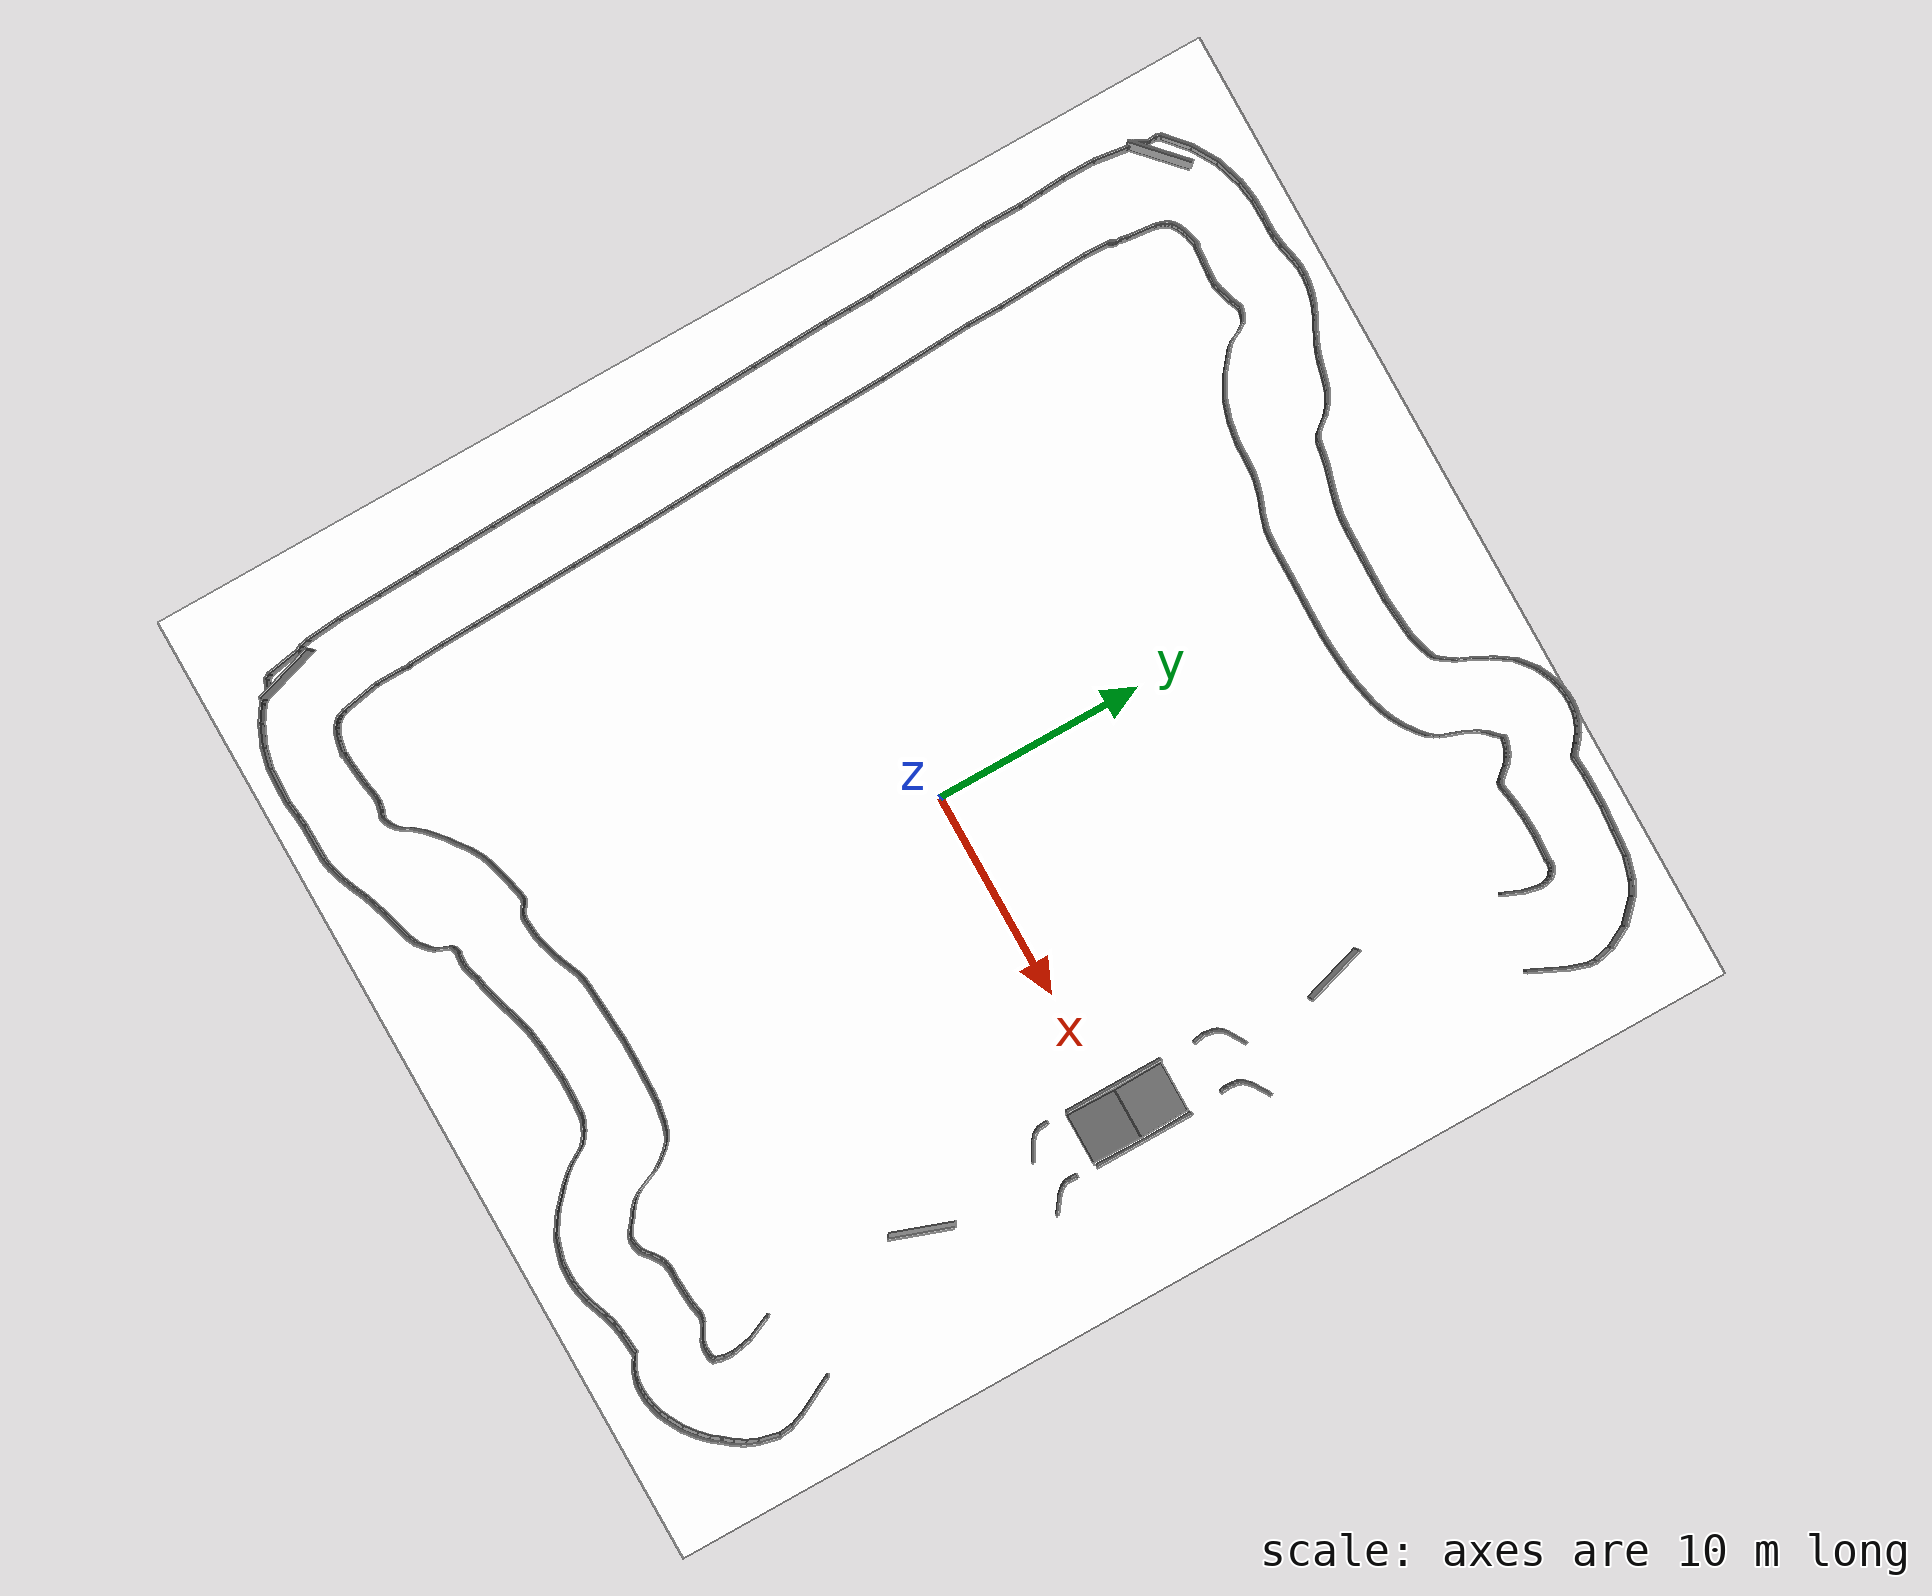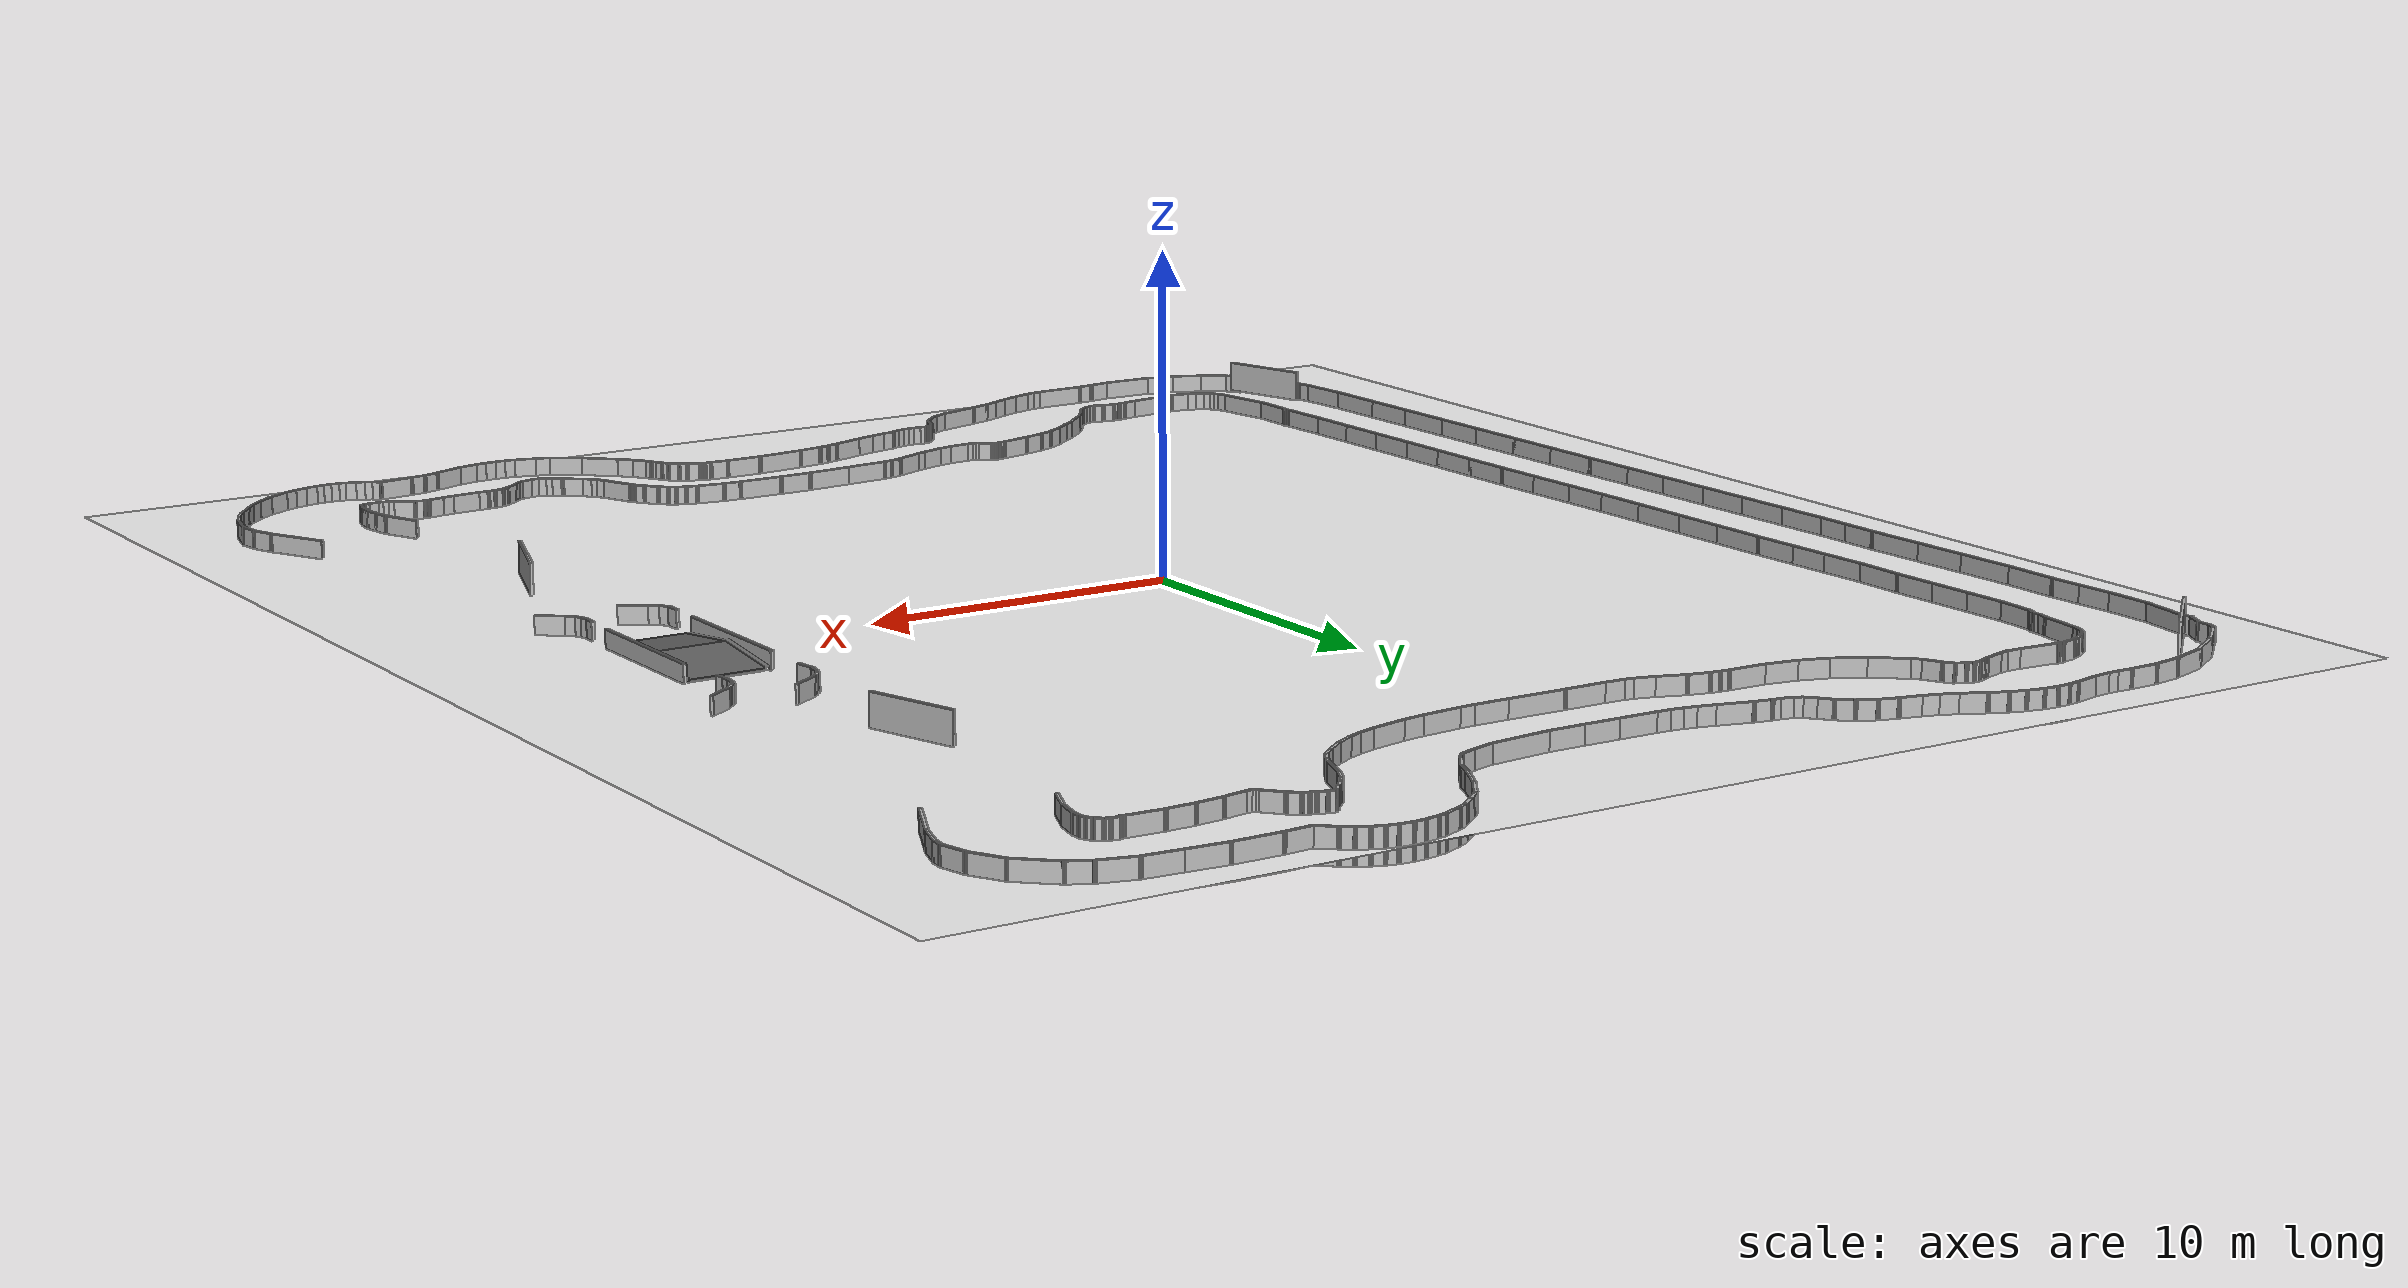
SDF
<sdf version="1.7">
 <world name="default">
  <physics name="1ms" type="ignored">
   <max_step_size>0.004</max_step_size>
   <real_time_factor>1.0</real_time_factor>
   <real_time_update_rate>250</real_time_update_rate>
  </physics>
  <scene><ambient>1 1 1 1</ambient><background>0.7 0.7 0.7 1</background><shadows>0</shadows></scene>
  <plugin filename="ignition-gazebo-physics-system" name="ignition::gazebo::systems::Physics"/>
  <plugin filename="ignition-gazebo-user-commands-system" name="ignition::gazebo::systems::UserCommands"/>
  <plugin filename="ignition-gazebo-scene-broadcaster-system" name="ignition::gazebo::systems::SceneBroadcaster"/>
  <light name="sun" type="directional">
   <cast_shadows>0</cast_shadows>
   <pose>0 0 10 0 -0 0</pose>
   <diffuse>1 1 1 1</diffuse>
   <specular>0.2 0.2 0.2 1</specular>
   <attenuation>
    <range>1000</range>
    <constant>0.9</constant>
    <linear>0.01</linear>
    <quadratic>0.001</quadratic>
   </attenuation>
   <direction>-0.5 0.1 -0.9</direction>
  </light>
  <model name="igvc_basic_ground">
   <static>true</static>
   <link name="link">
    <collision name="collision">
     <geometry><plane><normal>0 0 1</normal><size>47.512 52.864</size></plane></geometry>
     <surface><friction><ode><mu>100</mu><mu2>50</mu2></ode></friction></surface>
    </collision>
    <visual name="visual">
     <cast_shadows>false</cast_shadows>
     <geometry><plane><normal>0 0 1</normal><size>47.512 52.864</size></plane></geometry>
     <material>
      <ambient>1 1 1 1</ambient>
      <diffuse>1 1 1 1</diffuse>
      <specular>0 0 0 1</specular>
      <pbr><metal><albedo_map>IGVC_pavement.png</albedo_map><roughness>0.9</roughness></metal></pbr>
     </material>
    </visual>
   </link>
  </model>
  <spherical_coordinates>
   <surface_model>EARTH_WGS84</surface_model>
   <latitude_deg>0</latitude_deg>
   <longitude_deg>0</longitude_deg>
   <elevation>0</elevation>
   <heading_deg>0</heading_deg>
  </spherical_coordinates>
  <model name="barricade_1">
   <static>1</static>
   <pose>15.2038 11.26 0.5 0 0 1.8687</pose>
   <link name="link">
    <collision name="collision"><geometry><box><size>3 0.1 1</size></box></geometry></collision>
    <visual name="visual"><geometry><box><size>3 0.1 1</size></box></geometry></visual>
   </link>
  </model>
  <model name="barricade_2">
   <static>1</static>
   <pose>16.1541 -10.0442 0.5 0 0 1.2346</pose>
   <link name="link">
    <collision name="collision"><geometry><box><size>3 0.1 1</size></box></geometry></collision>
    <visual name="visual"><geometry><box><size>3 0.1 1</size></box></geometry></visual>
   </link>
  </model>
  <model name="barricade_3">
   <static>1</static>
   <pose>-18.8148 -22.3826 0.5 0 0 1.8687</pose>
   <link name="link">
    <collision name="collision"><geometry><box><size>3 0.1 1</size></box></geometry></collision>
    <visual name="visual"><geometry><box><size>3 0.1 1</size></box></geometry></visual>
   </link>
  </model>
  <model name="barricade_4">
   <static>1</static>
   <pose>-19.955 22.2029 0.5 0 0 0.753</pose>
   <link name="link">
    <collision name="collision"><geometry><box><size>3 0.1 1</size></box></geometry></collision>
    <visual name="visual"><geometry><box><size>3 0.1 1</size></box></geometry></visual>
   </link>
  </model>
  <model name="ramp_up">
   <static>1</static>
   <pose>16.1541 -0.8357 0.1 0.1122 0 0</pose>
   <link name="link">
    <collision name="collision">
     <geometry><box><size>2.41 2.41 0.1</size></box></geometry>
     <surface>
      <friction><ode><mu>100</mu><mu2>50</mu2><slip1>0.0</slip1><slip2>0.0</slip2></ode></friction>
     </surface>
    </collision>
    <visual name="visual">
     <geometry><box><size>2.41 2.41 0.1</size></box></geometry>
     <material><ambient>0.4 0.7 0.6 1</ambient><diffuse>0.4 0.4 0.4 1</diffuse></material>
    </visual>
   </link>
  </model>
  <model name="ramp_down">
   <static>1</static>
   <pose>16.1541 1.5493 0.1 0.1122 0 3.14</pose>
   <link name="link">
    <collision name="collision">
     <geometry><box><size>2.41 2.41 0.1</size></box></geometry>
     <surface>
      <friction><ode><mu>100</mu><mu2>50</mu2><slip1>0.0</slip1><slip2>0.0</slip2></ode></friction>
     </surface>
     <surface>
      <friction><ode><mu>100</mu><mu2>50</mu2><slip1>0.0</slip1><slip2>0.0</slip2></ode></friction>
     </surface>
    </collision>
    <visual name="visual">
     <geometry><box><size>2.41 2.41 0.1</size></box></geometry>
     <material><ambient>0.4 0.7 0.6 1</ambient><diffuse>0.4 0.4 0.4 1</diffuse></material>
    </visual>
   </link>
  </model>
  <model name="ramp_wall_left">
   <static>1</static>
   <pose>17.5091 0.4293 0 0 0 1.5708</pose>
   <link name="link">
    <collision name="collision"><geometry><box><size>4.78 0.1 1</size></box></geometry></collision>
    <visual name="visual"><geometry><box><size>4.78 0.1 1</size></box></geometry></visual>
   </link>
  </model>
  <model name="ramp_wall_right">
   <static>1</static>
   <pose>14.7941 0.4193 0 0 0 1.5708</pose>
   <link name="link">
    <collision name="collision"><geometry><box><size>4.78 0.1 1</size></box></geometry></collision>
    <visual name="visual"><geometry><box><size>4.78 0.1 1</size></box></geometry></visual>
   </link>
  </model>
  <model name="ramp_up_lane_line_left">
   <static>1</static>
   <pose>17.4091 -0.8357 0.1 0.1122 0 0</pose>
   <link name="link">
    <inertial><mass>0.1</mass><inertia><ixx>0.0001</ixx><iyy>0.0001</iyy><izz>0.0001</izz></inertia></inertial>
    <collision name="collision">
     <geometry><box><size>0.1 2.41 0.1</size></box></geometry>
     <surface><friction><ode><mu>0.1</mu><mu2>0.1</mu2></ode></friction></surface>
    </collision>
    <visual name="visual">
     <geometry><box><size>0.1 2.41 0.1</size></box></geometry>
     <material><ambient>1 1 1 1</ambient><diffuse>1 1 1 1</diffuse></material>
    </visual>
   </link>
  </model>
  <model name="ramp_up_lane_line_right">
   <static>1</static>
   <pose>14.8991 -0.8357 0.1 0.1122 0 0</pose>
   <link name="link">
    <inertial><mass>0.1</mass><inertia><ixx>0.0001</ixx><iyy>0.0001</iyy><izz>0.0001</izz></inertia></inertial>
    <collision name="collision">
     <geometry><box><size>0.1 2.41 0.1</size></box></geometry>
     <surface><friction><ode><mu>0.1</mu><mu2>0.1</mu2></ode></friction></surface>
    </collision>
    <visual name="visual">
     <geometry><box><size>0.1 2.41 0.1</size></box></geometry>
     <material><ambient>1 1 1 1</ambient><diffuse>1 1 1 1</diffuse></material>
    </visual>
   </link>
  </model>
  <model name="ramp_down_lane_line_left">
   <static>1</static>
   <pose>17.4091 1.5493 0.135 0.1122 0 3.14</pose>
   <link name="link">
    <inertial><mass>0.1</mass><inertia><ixx>0.0001</ixx><iyy>0.0001</iyy><izz>0.0001</izz></inertia></inertial>
    <collision name="collision">
     <geometry><box><size>0.1 2.41 0.1</size></box></geometry>
     <surface><friction><ode><mu>0.1</mu><mu2>0.1</mu2></ode></friction></surface>
    </collision>
    <visual name="visual">
     <geometry><box><size>0.1 2.41 0.1</size></box></geometry>
     <material><ambient>1 1 1 1</ambient><diffuse>1 1 1 1</diffuse></material>
    </visual>
   </link>
  </model>
  <model name="ramp_down_lane_line_right">
   <static>1</static>
   <pose>14.8991 1.5493 0.135 0.1122 0 3.14</pose>
   <link name="link">
    <inertial><mass>0.1</mass><inertia><ixx>0.0001</ixx><iyy>0.0001</iyy><izz>0.0001</izz></inertia></inertial>
    <collision name="collision">
     <geometry><box><size>0.1 2.41 0.1</size></box></geometry>
     <surface><friction><ode><mu>0.1</mu><mu2>0.1</mu2></ode></friction></surface>
    </collision>
    <visual name="visual">
     <geometry><box><size>0.1 2.41 0.1</size></box></geometry>
     <material><ambient>1 1 1 1</ambient><diffuse>1 1 1 1</diffuse></material>
    </visual>
   </link>
  </model>
  <model name="outer_wall_16">
   <static>1</static>
   <link name="link">
    <collision name="c0">
     <pose>17.3115 4.5705 0 0 0 1.73777</pose>
     <geometry><box><size>0.3472 0.1 1</size></box></geometry>
    </collision>
    <visual name="v0">
     <pose>17.3115 4.5705 0 0 0 1.73777</pose>
     <geometry><box><size>0.3472 0.1 1</size></box></geometry>
    </visual>
    <collision name="c1">
     <pose>17.2929 4.8402 0 0 0 1.55786</pose>
     <geometry><box><size>0.3957 0.1 1</size></box></geometry>
    </collision>
    <visual name="v1">
     <pose>17.2929 4.8402 0 0 0 1.55786</pose>
     <geometry><box><size>0.3957 0.1 1</size></box></geometry>
    </visual>
    <collision name="c2">
     <pose>17.3170 5.1400 0 0 0 1.42546</pose>
     <geometry><box><size>0.4072 0.1 1</size></box></geometry>
    </collision>
    <visual name="v2">
     <pose>17.3170 5.1400 0 0 0 1.42546</pose>
     <geometry><box><size>0.4072 0.1 1</size></box></geometry>
    </visual>
    <collision name="c3">
     <pose>17.3784 5.3875 0 0 0 1.18170</pose>
     <geometry><box><size>0.3064 0.1 1</size></box></geometry>
    </collision>
    <visual name="v3">
     <pose>17.3784 5.3875 0 0 0 1.18170</pose>
     <geometry><box><size>0.3064 0.1 1</size></box></geometry>
    </visual>
    <collision name="c4">
     <pose>17.5649 5.6326 0 0 0 0.79337</pose>
     <geometry><box><size>0.5200 0.1 1</size></box></geometry>
    </collision>
    <visual name="v4">
     <pose>17.5649 5.6326 0 0 0 0.79337</pose>
     <geometry><box><size>0.5200 0.1 1</size></box></geometry>
    </visual>
    <collision name="c5">
     <pose>18.0802 6.0149 0 0 0 0.56379</pose>
     <geometry><box><size>0.9708 0.1 1</size></box></geometry>
    </collision>
    <visual name="v5">
     <pose>18.0802 6.0149 0 0 0 0.56379</pose>
     <geometry><box><size>0.9708 0.1 1</size></box></geometry>
    </visual>
   </link>
  </model>
  <model name="outer_wall_17">
   <static>1</static>
   <link name="link">
    <collision name="c0">
     <pose>17.4446 -3.1479 0 0 0 -1.65022</pose>
     <geometry><box><size>0.4533 0.1 1</size></box></geometry>
    </collision>
    <visual name="v0">
     <pose>17.4446 -3.1479 0 0 0 -1.65022</pose>
     <geometry><box><size>0.4533 0.1 1</size></box></geometry>
    </visual>
    <collision name="c1">
     <pose>17.4621 -3.4520 0 0 0 -1.32872</pose>
     <geometry><box><size>0.3637 0.1 1</size></box></geometry>
    </collision>
    <visual name="v1">
     <pose>17.4621 -3.4520 0 0 0 -1.32872</pose>
     <geometry><box><size>0.3637 0.1 1</size></box></geometry>
    </visual>
    <collision name="c2">
     <pose>17.5405 -3.6717 0 0 0 -1.09983</pose>
     <geometry><box><size>0.3058 0.1 1</size></box></geometry>
    </collision>
    <visual name="v2">
     <pose>17.5405 -3.6717 0 0 0 -1.09983</pose>
     <geometry><box><size>0.3058 0.1 1</size></box></geometry>
    </visual>
    <collision name="c3">
     <pose>17.6985 -3.8836 0 0 0 -0.82344</pose>
     <geometry><box><size>0.4277 0.1 1</size></box></geometry>
    </collision>
    <visual name="v3">
     <pose>17.6985 -3.8836 0 0 0 -0.82344</pose>
     <geometry><box><size>0.4277 0.1 1</size></box></geometry>
    </visual>
    <collision name="c4">
     <pose>18.1457 -4.2514 0 0 0 -0.63536</pose>
     <geometry><box><size>0.9345 0.1 1</size></box></geometry>
    </collision>
    <visual name="v4">
     <pose>18.1457 -4.2514 0 0 0 -0.63536</pose>
     <geometry><box><size>0.9345 0.1 1</size></box></geometry>
    </visual>
   </link>
  </model>
  <model name="inner_wall_1">
   <static>1</static>
   <link name="link">
    <collision name="c0">
     <pose>14.8047 4.7719 0 0 0 1.73334</pose>
     <geometry><box><size>0.6514 0.1 1</size></box></geometry>
    </collision>
    <visual name="v0">
     <pose>14.8047 4.7719 0 0 0 1.73334</pose>
     <geometry><box><size>0.6514 0.1 1</size></box></geometry>
    </visual>
    <collision name="c1">
     <pose>14.7986 5.2560 0 0 0 1.39106</pose>
     <geometry><box><size>0.5309 0.1 1</size></box></geometry>
    </collision>
    <visual name="v1">
     <pose>14.7986 5.2560 0 0 0 1.39106</pose>
     <geometry><box><size>0.5309 0.1 1</size></box></geometry>
    </visual>
    <collision name="c2">
     <pose>14.8745 5.5638 0 0 0 1.19883</pose>
     <geometry><box><size>0.3056 0.1 1</size></box></geometry>
    </collision>
    <visual name="v2">
     <pose>14.8745 5.5638 0 0 0 1.19883</pose>
     <geometry><box><size>0.3056 0.1 1</size></box></geometry>
    </visual>
    <collision name="c3">
     <pose>14.9716 5.7363 0 0 0 0.90945</pose>
     <geometry><box><size>0.2945 0.1 1</size></box></geometry>
    </collision>
    <visual name="v3">
     <pose>14.9716 5.7363 0 0 0 0.90945</pose>
     <geometry><box><size>0.2945 0.1 1</size></box></geometry>
    </visual>
    <collision name="c4">
     <pose>15.1278 5.8947 0 0 0 0.70249</pose>
     <geometry><box><size>0.3526 0.1 1</size></box></geometry>
    </collision>
    <visual name="v4">
     <pose>15.1278 5.8947 0 0 0 0.70249</pose>
     <geometry><box><size>0.3526 0.1 1</size></box></geometry>
    </visual>
    <collision name="c5">
     <pose>15.5881 6.1968 0 0 0 0.54477</pose>
     <geometry><box><size>0.9512 0.1 1</size></box></geometry>
    </collision>
    <visual name="v5">
     <pose>15.5881 6.1968 0 0 0 0.54477</pose>
     <geometry><box><size>0.9512 0.1 1</size></box></geometry>
    </visual>
   </link>
  </model>
  <model name="inner_wall_2">
   <static>1</static>
   <link name="link">
    <collision name="c0">
     <pose>14.7838 -3.1799 0 0 0 -1.51195</pose>
     <geometry><box><size>0.5169 0.1 1</size></box></geometry>
    </collision>
    <visual name="v0">
     <pose>14.7838 -3.1799 0 0 0 -1.51195</pose>
     <geometry><box><size>0.5169 0.1 1</size></box></geometry>
    </visual>
    <collision name="c1">
     <pose>14.8763 -3.5304 0 0 0 -1.05760</pose>
     <geometry><box><size>0.4269 0.1 1</size></box></geometry>
    </collision>
    <visual name="v1">
     <pose>14.8763 -3.5304 0 0 0 -1.05760</pose>
     <geometry><box><size>0.4269 0.1 1</size></box></geometry>
    </visual>
    <collision name="c2">
     <pose>15.0863 -3.7819 0 0 0 -0.69927</pose>
     <geometry><box><size>0.4391 0.1 1</size></box></geometry>
    </collision>
    <visual name="v2">
     <pose>15.0863 -3.7819 0 0 0 -0.69927</pose>
     <geometry><box><size>0.4391 0.1 1</size></box></geometry>
    </visual>
    <collision name="c3">
     <pose>15.5841 -4.0953 0 0 0 -0.50652</pose>
     <geometry><box><size>0.9418 0.1 1</size></box></geometry>
    </collision>
    <visual name="v3">
     <pose>15.5841 -4.0953 0 0 0 -0.50652</pose>
     <geometry><box><size>0.9418 0.1 1</size></box></geometry>
    </visual>
   </link>
  </model>
  <model name="outer_lane_wall">
   <static>1</static>
   <link name="link">
    <collision name="c0">
     <pose>19.6899 19.5977 0 0 0 1.128</pose>
     <geometry><box><size>1.9502 0.1 1</size></box></geometry>
    </collision>
    <visual name="v0">
     <pose>19.6899 19.5977 0 0 0 1.128</pose>
     <geometry><box><size>1.9502 0.1 1</size></box></geometry>
    </visual>
    <collision name="c1">
     <pose>20.2228 20.848 0 0 0 1.2522</pose>
     <geometry><box><size>0.9806 0.1 1</size></box></geometry>
    </collision>
    <visual name="v1">
     <pose>20.2228 20.848 0 0 0 1.2522</pose>
     <geometry><box><size>0.9806 0.1 1</size></box></geometry>
    </visual>
    <collision name="c2">
     <pose>20.3851 21.456 0 0 0 1.4405</pose>
     <geometry><box><size>0.4928 0.1 1</size></box></geometry>
    </collision>
    <visual name="v2">
     <pose>20.3851 21.456 0 0 0 1.4405</pose>
     <geometry><box><size>0.4928 0.1 1</size></box></geometry>
    </visual>
    <collision name="c3">
     <pose>20.3142 22.08 0 0 0 1.7896</pose>
     <geometry><box><size>0.9902 0.1 1</size></box></geometry>
    </collision>
    <visual name="v3">
     <pose>20.3142 22.08 0 0 0 1.7896</pose>
     <geometry><box><size>0.9902 0.1 1</size></box></geometry>
    </visual>
    <collision name="c4">
     <pose>19.9529 23.008 0 0 0 2.0619</pose>
     <geometry><box><size>1.2280 0.1 1</size></box></geometry>
    </collision>
    <visual name="v4">
     <pose>19.9529 23.008 0 0 0 2.0619</pose>
     <geometry><box><size>1.2280 0.1 1</size></box></geometry>
    </visual>
    <collision name="c5">
     <pose>19.1846 23.9771 0 0 0 2.3869</pose>
     <geometry><box><size>1.4809 0.1 1</size></box></geometry>
    </collision>
    <visual name="v5">
     <pose>19.1846 23.9771 0 0 0 2.3869</pose>
     <geometry><box><size>1.4809 0.1 1</size></box></geometry>
    </visual>
    <collision name="c6">
     <pose>18.3613 24.6172 0 0 0 2.6612</pose>
     <geometry><box><size>0.8191 0.1 1</size></box></geometry>
    </collision>
    <visual name="v6">
     <pose>18.3613 24.6172 0 0 0 2.6612</pose>
     <geometry><box><size>0.8191 0.1 1</size></box></geometry>
    </visual>
    <collision name="c7">
     <pose>17.5066 24.9380 0 0 0 2.87008</pose>
     <geometry><box><size>1.2127 0.1 1</size></box></geometry>
    </collision>
    <visual name="v7">
     <pose>17.5066 24.9380 0 0 0 2.87008</pose>
     <geometry><box><size>1.2127 0.1 1</size></box></geometry>
    </visual>
    <collision name="c8">
     <pose>16.3598 25.1324 0 0 0 3.06763</pose>
     <geometry><box><size>1.3251 0.1 1</size></box></geometry>
    </collision>
    <visual name="v8">
     <pose>16.3598 25.1324 0 0 0 3.06763</pose>
     <geometry><box><size>1.3251 0.1 1</size></box></geometry>
    </visual>
    <collision name="c9">
     <pose>15.1381 25.2230 0 0 0 3.06763</pose>
     <geometry><box><size>1.3251 0.1 1</size></box></geometry>
    </collision>
    <visual name="v9">
     <pose>15.1381 25.2230 0 0 0 3.06763</pose>
     <geometry><box><size>1.3251 0.1 1</size></box></geometry>
    </visual>
    <collision name="c10">
     <pose>13.7522 25.2668 0 0 0 -3.13970</pose>
     <geometry><box><size>1.6502 0.1 1</size></box></geometry>
    </collision>
    <visual name="v10">
     <pose>13.7522 25.2668 0 0 0 -3.13970</pose>
     <geometry><box><size>1.6502 0.1 1</size></box></geometry>
    </visual>
    <collision name="c11">
     <pose>12.5277 25.2361 0 0 0 -3.07660</pose>
     <geometry><box><size>1.0005 0.1 1</size></box></geometry>
    </collision>
    <visual name="v11">
     <pose>12.5277 25.2361 0 0 0 -3.07660</pose>
     <geometry><box><size>1.0005 0.1 1</size></box></geometry>
    </visual>
    <collision name="c12">
     <pose>11.8377 25.4110 0 0 0 2.43798</pose>
     <geometry><box><size>0.7313 0.1 1</size></box></geometry>
    </collision>
    <visual name="v12">
     <pose>11.8377 25.4110 0 0 0 2.43798</pose>
     <geometry><box><size>0.7313 0.1 1</size></box></geometry>
    </visual>
    <collision name="c13">
     <pose>11.4379 25.7339 0 0 0 2.50108</pose>
     <geometry><box><size>0.4970 0.1 1</size></box></geometry>
    </collision>
    <visual name="v13">
     <pose>11.4379 25.7339 0 0 0 2.50108</pose>
     <geometry><box><size>0.4970 0.1 1</size></box></geometry>
    </visual>
    <collision name="c14">
     <pose>11.1160 25.9422 0 0 0 2.63777</pose>
     <geometry><box><size>0.4715 0.1 1</size></box></geometry>
    </collision>
    <visual name="v14">
     <pose>11.1160 25.9422 0 0 0 2.63777</pose>
     <geometry><box><size>0.4715 0.1 1</size></box></geometry>
    </visual>
    <collision name="c15">
     <pose>10.7856 26.1008 0 0 0 2.75169</pose>
     <geometry><box><size>0.4628 0.1 1</size></box></geometry>
    </collision>
    <visual name="v15">
     <pose>10.7856 26.1008 0 0 0 2.75169</pose>
     <geometry><box><size>0.4628 0.1 1</size></box></geometry>
    </visual>
    <collision name="c16">
     <pose>10.4503 26.2085 0 0 0 2.91462</pose>
     <geometry><box><size>0.4439 0.1 1</size></box></geometry>
    </collision>
    <visual name="v16">
     <pose>10.4503 26.2085 0 0 0 2.91462</pose>
     <geometry><box><size>0.4439 0.1 1</size></box></geometry>
    </visual>
    <collision name="c17">
     <pose>10.0685 26.2667 0 0 0 3.05078</pose>
     <geometry><box><size>0.5304 0.1 1</size></box></geometry>
    </collision>
    <visual name="v17">
     <pose>10.0685 26.2667 0 0 0 3.05078</pose>
     <geometry><box><size>0.5304 0.1 1</size></box></geometry>
    </visual>
    <collision name="c18">
     <pose>9.6784 26.2787 0 0 0 -3.09912</pose>
     <geometry><box><size>0.4518 0.1 1</size></box></geometry>
    </collision>
    <visual name="v18">
     <pose>9.6784 26.2787 0 0 0 -3.09912</pose>
     <geometry><box><size>0.4518 0.1 1</size></box></geometry>
    </visual>
    <collision name="c19">
     <pose>9.2860 26.2366 0 0 0 -2.98306</pose>
     <geometry><box><size>0.5388 0.1 1</size></box></geometry>
    </collision>
    <visual name="v19">
     <pose>9.2860 26.2366 0 0 0 -2.98306</pose>
     <geometry><box><size>0.5388 0.1 1</size></box></geometry>
    </visual>
    <collision name="c20">
     <pose>8.9286 26.1686 0 0 0 -2.90892</pose>
     <geometry><box><size>0.3894 0.1 1</size></box></geometry>
    </collision>
    <visual name="v20">
     <pose>8.9286 26.1686 0 0 0 -2.90892</pose>
     <geometry><box><size>0.3894 0.1 1</size></box></geometry>
    </visual>
    <collision name="c21">
     <pose>8.4938 26.0124 0 0 0 -2.74576</pose>
     <geometry><box><size>0.7372 0.1 1</size></box></geometry>
    </collision>
    <visual name="v21">
     <pose>8.4938 26.0124 0 0 0 -2.74576</pose>
     <geometry><box><size>0.7372 0.1 1</size></box></geometry>
    </visual>
    <collision name="c22">
     <pose>8.0288 25.8037 0 0 0 -2.67615</pose>
     <geometry><box><size>0.4828 0.1 1</size></box></geometry>
    </collision>
    <visual name="v22">
     <pose>8.0288 25.8037 0 0 0 -2.67615</pose>
     <geometry><box><size>0.4828 0.1 1</size></box></geometry>
    </visual>
    <collision name="c23">
     <pose>7.6093 25.5204 0 0 0 -2.47037</pose>
     <geometry><box><size>0.7346 0.1 1</size></box></geometry>
    </collision>
    <visual name="v23">
     <pose>7.6093 25.5204 0 0 0 -2.47037</pose>
     <geometry><box><size>0.7346 0.1 1</size></box></geometry>
    </visual>
    <collision name="c24">
     <pose>7.2088 25.1896 0 0 0 -2.42126</pose>
     <geometry><box><size>0.5046 0.1 1</size></box></geometry>
    </collision>
    <visual name="v24">
     <pose>7.2088 25.1896 0 0 0 -2.42126</pose>
     <geometry><box><size>0.5046 0.1 1</size></box></geometry>
    </visual>
    <collision name="c25">
     <pose>6.7743 24.6391 0 0 0 -2.16599</pose>
     <geometry><box><size>1.1075 0.1 1</size></box></geometry>
    </collision>
    <visual name="v25">
     <pose>6.7743 24.6391 0 0 0 -2.16599</pose>
     <geometry><box><size>1.1075 0.1 1</size></box></geometry>
    </visual>
    <collision name="c26">
     <pose>6.2631 23.7706 0 0 0 -2.04004</pose>
     <geometry><box><size>1.1121 0.1 1</size></box></geometry>
    </collision>
    <visual name="v26">
     <pose>6.2631 23.7706 0 0 0 -2.04004</pose>
     <geometry><box><size>1.1121 0.1 1</size></box></geometry>
    </visual>
    <collision name="c27">
     <pose>5.9380 23.0858 0 0 0 -1.96158</pose>
     <geometry><box><size>0.6051 0.1 1</size></box></geometry>
    </collision>
    <visual name="v27">
     <pose>5.9380 23.0858 0 0 0 -1.96158</pose>
     <geometry><box><size>0.6051 0.1 1</size></box></geometry>
    </visual>
    <collision name="c28">
     <pose>5.6384 22.5508 0 0 0 -2.16445</pose>
     <geometry><box><size>0.8272 0.1 1</size></box></geometry>
    </collision>
    <visual name="v28">
     <pose>5.6384 22.5508 0 0 0 -2.16445</pose>
     <geometry><box><size>0.8272 0.1 1</size></box></geometry>
    </visual>
    <collision name="c29">
     <pose>5.3409 22.1334 0 0 0 -2.25260</pose>
     <geometry><box><size>0.3988 0.1 1</size></box></geometry>
    </collision>
    <visual name="v29">
     <pose>5.3409 22.1334 0 0 0 -2.25260</pose>
     <geometry><box><size>0.3988 0.1 1</size></box></geometry>
    </visual>
    <collision name="c30">
     <pose>5.2107 21.9842 0 0 0 -2.39551</pose>
     <geometry><box><size>0.1980 0.1 1</size></box></geometry>
    </collision>
    <visual name="v30">
     <pose>5.2107 21.9842 0 0 0 -2.39551</pose>
     <geometry><box><size>0.1980 0.1 1</size></box></geometry>
    </visual>
    <collision name="c31">
     <pose>4.9246 21.8544 0 0 0 -2.77349</pose>
     <geometry><box><size>0.6362 0.1 1</size></box></geometry>
    </collision>
    <visual name="v31">
     <pose>4.9246 21.8544 0 0 0 -2.77349</pose>
     <geometry><box><size>0.6362 0.1 1</size></box></geometry>
    </visual>
    <collision name="c32">
     <pose>4.3143 21.6536 0 0 0 -2.85957</pose>
     <geometry><box><size>0.8499 0.1 1</size></box></geometry>
    </collision>
    <visual name="v32">
     <pose>4.3143 21.6536 0 0 0 -2.85957</pose>
     <geometry><box><size>0.8499 0.1 1</size></box></geometry>
    </visual>
    <collision name="c33">
     <pose>2.9588 21.4577 0 0 0 -3.04987</pose>
     <geometry><box><size>2.0991 0.1 1</size></box></geometry>
    </collision>
    <visual name="v33">
     <pose>2.9588 21.4577 0 0 0 -3.04987</pose>
     <geometry><box><size>2.0991 0.1 1</size></box></geometry>
    </visual>
    <collision name="c34">
     <pose>1.3887 21.3678 0 0 0 3.13875</pose>
     <geometry><box><size>1.2496 0.1 1</size></box></geometry>
    </collision>
    <visual name="v34">
     <pose>1.3887 21.3678 0 0 0 3.13875</pose>
     <geometry><box><size>1.2496 0.1 1</size></box></geometry>
    </visual>
    <collision name="c35">
     <pose>0.2140 21.3792 0 0 0 3.12521</pose>
     <geometry><box><size>1.2999 0.1 1</size></box></geometry>
    </collision>
    <visual name="v35">
     <pose>0.2140 21.3792 0 0 0 3.12521</pose>
     <geometry><box><size>1.2999 0.1 1</size></box></geometry>
    </visual>
    <collision name="c36">
     <pose>-0.9858 21.3989 0 0 0 3.12521</pose>
     <geometry><box><size>1.2999 0.1 1</size></box></geometry>
    </collision>
    <visual name="v36">
     <pose>-0.9858 21.3989 0 0 0 3.12521</pose>
     <geometry><box><size>1.2999 0.1 1</size></box></geometry>
    </visual>
    <collision name="c37">
     <pose>-1.8099 21.4206 0 0 0 3.08880</pose>
     <geometry><box><size>0.5492 0.1 1</size></box></geometry>
    </collision>
    <visual name="v37">
     <pose>-1.8099 21.4206 0 0 0 3.08880</pose>
     <geometry><box><size>0.5492 0.1 1</size></box></geometry>
    </visual>
    <collision name="c38">
     <pose>-2.2325 21.4590 0 0 0 3.00830</pose>
     <geometry><box><size>0.5002 0.1 1</size></box></geometry>
    </collision>
    <visual name="v38">
     <pose>-2.2325 21.4590 0 0 0 3.00830</pose>
     <geometry><box><size>0.5002 0.1 1</size></box></geometry>
    </visual>
    <collision name="c39">
     <pose>-2.6287 21.5229 0 0 0 2.95541</pose>
     <geometry><box><size>0.5027 0.1 1</size></box></geometry>
    </collision>
    <visual name="v39">
     <pose>-2.6287 21.5229 0 0 0 2.95541</pose>
     <geometry><box><size>0.5027 0.1 1</size></box></geometry>
    </visual>
    <collision name="c40">
     <pose>-3.0961 21.6272 0 0 0 2.89789</pose>
     <geometry><box><size>0.6555 0.1 1</size></box></geometry>
    </collision>
    <visual name="v40">
     <pose>-3.0961 21.6272 0 0 0 2.89789</pose>
     <geometry><box><size>0.6555 0.1 1</size></box></geometry>
    </visual>
    <collision name="c41">
     <pose>-3.8904 21.8437 0 0 0 2.86405</pose>
     <geometry><box><size>1.1912 0.1 1</size></box></geometry>
    </collision>
    <visual name="v41">
     <pose>-3.8904 21.8437 0 0 0 2.86405</pose>
     <geometry><box><size>1.1912 0.1 1</size></box></geometry>
    </visual>
    <collision name="c42">
     <pose>-4.6870 22.0488 0 0 0 2.93983</pose>
     <geometry><box><size>0.6551 0.1 1</size></box></geometry>
    </collision>
    <visual name="v42">
     <pose>-4.6870 22.0488 0 0 0 2.93983</pose>
     <geometry><box><size>0.6551 0.1 1</size></box></geometry>
    </visual>
    <collision name="c43">
     <pose>-5.0906 22.1204 0 0 0 3.02113</pose>
     <geometry><box><size>0.3652 0.1 1</size></box></geometry>
    </collision>
    <visual name="v43">
     <pose>-5.0906 22.1204 0 0 0 3.02113</pose>
     <geometry><box><size>0.3652 0.1 1</size></box></geometry>
    </visual>
    <collision name="c44">
     <pose>-5.4160 22.1747 0 0 0 2.94586</pose>
     <geometry><box><size>0.4950 0.1 1</size></box></geometry>
    </collision>
    <visual name="v44">
     <pose>-5.4160 22.1747 0 0 0 2.94586</pose>
     <geometry><box><size>0.4950 0.1 1</size></box></geometry>
    </visual>
    <collision name="c45">
     <pose>-5.7277 22.2825 0 0 0 2.61038</pose>
     <geometry><box><size>0.3737 0.1 1</size></box></geometry>
    </collision>
    <visual name="v45">
     <pose>-5.7277 22.2825 0 0 0 2.61038</pose>
     <geometry><box><size>0.3737 0.1 1</size></box></geometry>
    </visual>
    <collision name="c46">
     <pose>-5.9743 22.4937 0 0 0 2.30665</pose>
     <geometry><box><size>0.4830 0.1 1</size></box></geometry>
    </collision>
    <visual name="v46">
     <pose>-5.9743 22.4937 0 0 0 2.30665</pose>
     <geometry><box><size>0.4830 0.1 1</size></box></geometry>
    </visual>
    <collision name="c47">
     <pose>-6.2427 22.8141 0 0 0 2.23557</pose>
     <geometry><box><size>0.5536 0.1 1</size></box></geometry>
    </collision>
    <visual name="v47">
     <pose>-6.2427 22.8141 0 0 0 2.23557</pose>
     <geometry><box><size>0.5536 0.1 1</size></box></geometry>
    </visual>
    <collision name="c48">
     <pose>-6.5930 23.1738 0 0 0 2.43094</pose>
     <geometry><box><size>0.6553 0.1 1</size></box></geometry>
    </collision>
    <visual name="v48">
     <pose>-6.5930 23.1738 0 0 0 2.43094</pose>
     <geometry><box><size>0.6553 0.1 1</size></box></geometry>
    </visual>
    <collision name="c49">
     <pose>-7.0705 23.4913 0 0 0 2.66932</pose>
     <geometry><box><size>0.6997 0.1 1</size></box></geometry>
    </collision>
    <visual name="v49">
     <pose>-7.0705 23.4913 0 0 0 2.66932</pose>
     <geometry><box><size>0.6997 0.1 1</size></box></geometry>
    </visual>
    <collision name="c50">
     <pose>-7.6239 23.7168 0 0 0 2.83985</pose>
     <geometry><box><size>0.7000 0.1 1</size></box></geometry>
    </collision>
    <visual name="v50">
     <pose>-7.6239 23.7168 0 0 0 2.83985</pose>
     <geometry><box><size>0.7000 0.1 1</size></box></geometry>
    </visual>
    <collision name="c51">
     <pose>-8.2510 23.8874 0 0 0 2.90693</pose>
     <geometry><box><size>0.8004 0.1 1</size></box></geometry>
    </collision>
    <visual name="v51">
     <pose>-8.2510 23.8874 0 0 0 2.90693</pose>
     <geometry><box><size>0.8004 0.1 1</size></box></geometry>
    </visual>
    <collision name="c52">
     <pose>-8.8316 24.0425 0 0 0 2.84397</pose>
     <geometry><box><size>0.6021 0.1 1</size></box></geometry>
    </collision>
    <visual name="v52">
     <pose>-8.8316 24.0425 0 0 0 2.84397</pose>
     <geometry><box><size>0.6021 0.1 1</size></box></geometry>
    </visual>
    <collision name="c53">
     <pose>-9.3300 24.2234 0 0 0 2.74783</pose>
     <geometry><box><size>0.6597 0.1 1</size></box></geometry>
    </collision>
    <visual name="v53">
     <pose>-9.3300 24.2234 0 0 0 2.74783</pose>
     <geometry><box><size>0.6597 0.1 1</size></box></geometry>
    </visual>
    <collision name="c54">
     <pose>-9.9385 24.5147 0 0 0 2.65799</pose>
     <geometry><box><size>0.8909 0.1 1</size></box></geometry>
    </collision>
    <visual name="v54">
     <pose>-9.9385 24.5147 0 0 0 2.65799</pose>
     <geometry><box><size>0.8909 0.1 1</size></box></geometry>
    </visual>
    <collision name="c55">
     <pose>-10.5538 24.8189 0 0 0 2.71540</pose>
     <geometry><box><size>0.6825 0.1 1</size></box></geometry>
    </collision>
    <visual name="v55">
     <pose>-10.5538 24.8189 0 0 0 2.71540</pose>
     <geometry><box><size>0.6825 0.1 1</size></box></geometry>
    </visual>
    <collision name="c56">
     <pose>-11.0594 25.0194 0 0 0 2.81999</pose>
     <geometry><box><size>0.6068 0.1 1</size></box></geometry>
    </collision>
    <visual name="v56">
     <pose>-11.0594 25.0194 0 0 0 2.81999</pose>
     <geometry><box><size>0.6068 0.1 1</size></box></geometry>
    </visual>
    <collision name="c57">
     <pose>-11.5689 25.1561 0 0 0 2.93439</pose>
     <geometry><box><size>0.6500 0.1 1</size></box></geometry>
    </collision>
    <visual name="v57">
     <pose>-11.5689 25.1561 0 0 0 2.93439</pose>
     <geometry><box><size>0.6500 0.1 1</size></box></geometry>
    </visual>
    <collision name="c58">
     <pose>-12.0643 25.2334 0 0 0 3.05030</pose>
     <geometry><box><size>0.5544 0.1 1</size></box></geometry>
    </collision>
    <visual name="v58">
     <pose>-12.0643 25.2334 0 0 0 3.05030</pose>
     <geometry><box><size>0.5544 0.1 1</size></box></geometry>
    </visual>
    <collision name="c59">
     <pose>-12.5010 25.2492 0 0 0 -3.11842</pose>
     <geometry><box><size>0.5209 0.1 1</size></box></geometry>
    </collision>
    <visual name="v59">
     <pose>-12.5010 25.2492 0 0 0 -3.11842</pose>
     <geometry><box><size>0.5209 0.1 1</size></box></geometry>
    </visual>
    <collision name="c60">
     <pose>-12.8968 25.2131 0 0 0 -2.97492</pose>
     <geometry><box><size>0.4761 0.1 1</size></box></geometry>
    </collision>
    <visual name="v60">
     <pose>-12.8968 25.2131 0 0 0 -2.97492</pose>
     <geometry><box><size>0.4761 0.1 1</size></box></geometry>
    </visual>
    <collision name="c61">
     <pose>-13.4942 25.0904 0 0 0 -2.92290</pose>
     <geometry><box><size>0.9442 0.1 1</size></box></geometry>
    </collision>
    <visual name="v61">
     <pose>-13.4942 25.0904 0 0 0 -2.92290</pose>
     <geometry><box><size>0.9442 0.1 1</size></box></geometry>
    </visual>
    <collision name="c62">
     <pose>-14.1855 24.9637 0 0 0 -3.01659</pose>
     <geometry><box><size>0.6627 0.1 1</size></box></geometry>
    </collision>
    <visual name="v62">
     <pose>-14.1855 24.9637 0 0 0 -3.01659</pose>
     <geometry><box><size>0.6627 0.1 1</size></box></geometry>
    </visual>
    <collision name="c63">
     <pose>-14.6409 24.9234 0 0 0 -3.11188</pose>
     <geometry><box><size>0.4527 0.1 1</size></box></geometry>
    </collision>
    <visual name="v63">
     <pose>-14.6409 24.9234 0 0 0 -3.11188</pose>
     <geometry><box><size>0.4527 0.1 1</size></box></geometry>
    </visual>
    <collision name="c64">
     <pose>-15.0678 24.9266 0 0 0 3.10788</pose>
     <geometry><box><size>0.6016 0.1 1</size></box></geometry>
    </collision>
    <visual name="v64">
     <pose>-15.0678 24.9266 0 0 0 3.10788</pose>
     <geometry><box><size>0.6016 0.1 1</size></box></geometry>
    </visual>
    <collision name="c65">
     <pose>-15.7940 24.9270 0 0 0 -3.12472</pose>
     <geometry><box><size>1.0513 0.1 1</size></box></geometry>
    </collision>
    <visual name="v65">
     <pose>-15.7940 24.9270 0 0 0 -3.12472</pose>
     <geometry><box><size>1.0513 0.1 1</size></box></geometry>
    </visual>
    <collision name="c66">
     <pose>-16.7391 24.8448 0 0 0 -2.98471</pose>
     <geometry><box><size>1.0506 0.1 1</size></box></geometry>
    </collision>
    <visual name="v66">
     <pose>-16.7391 24.8448 0 0 0 -2.98471</pose>
     <geometry><box><size>1.0506 0.1 1</size></box></geometry>
    </visual>
    <collision name="c67">
     <pose>-17.8499 24.5627 0 0 0 -2.82826</pose>
     <geometry><box><size>1.4484 0.1 1</size></box></geometry>
    </collision>
    <visual name="v67">
     <pose>-17.8499 24.5627 0 0 0 -2.82826</pose>
     <geometry><box><size>1.4484 0.1 1</size></box></geometry>
    </visual>
    <collision name="c68">
     <pose>-19.0497 24.0137 0 0 0 -2.6014</pose>
     <geometry><box><size>1.4041 0.1 1</size></box></geometry>
    </collision>
    <visual name="v68">
     <pose>-19.0497 24.0137 0 0 0 -2.6014</pose>
     <geometry><box><size>1.4041 0.1 1</size></box></geometry>
    </visual>
    <collision name="c69">
     <pose>-20.1427 23.2045 0 0 0 -2.4155</pose>
     <geometry><box><size>1.5245 0.1 1</size></box></geometry>
    </collision>
    <visual name="v69">
     <pose>-20.1427 23.2045 0 0 0 -2.4155</pose>
     <geometry><box><size>1.5245 0.1 1</size></box></geometry>
    </visual>
    <collision name="c70">
     <pose>-20.719 22.6057 0 0 0 -1.9036</pose>
     <geometry><box><size>0.3704 0.1 1</size></box></geometry>
    </collision>
    <visual name="v70">
     <pose>-20.719 22.6057 0 0 0 -1.9036</pose>
     <geometry><box><size>0.3704 0.1 1</size></box></geometry>
    </visual>
    <collision name="c71">
     <pose>-20.7511 22.288 0 0 0 -1.5113</pose>
     <geometry><box><size>0.4904 0.1 1</size></box></geometry>
    </collision>
    <visual name="v71">
     <pose>-20.7511 22.288 0 0 0 -1.5113</pose>
     <geometry><box><size>0.4904 0.1 1</size></box></geometry>
    </visual>
    <collision name="c72">
     <pose>-20.8837 21.792 0 0 0 -2.0134</pose>
     <geometry><box><size>0.7763 0.1 1</size></box></geometry>
    </collision>
    <visual name="v72">
     <pose>-20.8837 21.792 0 0 0 -2.0134</pose>
     <geometry><box><size>0.7763 0.1 1</size></box></geometry>
    </visual>
    <collision name="c73">
     <pose>-20.9912 21.3441 0 0 0 -1.322</pose>
     <geometry><box><size>0.4022 0.1 1</size></box></geometry>
    </collision>
    <visual name="v73">
     <pose>-20.9912 21.3441 0 0 0 -1.322</pose>
     <geometry><box><size>0.4022 0.1 1</size></box></geometry>
    </visual>
    <collision name="c74">
     <pose>-21.0666 20.4 0 0 0 -1.71</pose>
     <geometry><box><size>1.7211 0.1 1</size></box></geometry>
    </collision>
    <visual name="v74">
     <pose>-21.0666 20.4 0 0 0 -1.71</pose>
     <geometry><box><size>1.7211 0.1 1</size></box></geometry>
    </visual>
    <collision name="c75">
     <pose>-21.1787 18.832 0 0 0 -1.5708</pose>
     <geometry><box><size>1.6417 0.1 1</size></box></geometry>
    </collision>
    <visual name="v75">
     <pose>-21.1787 18.832 0 0 0 -1.5708</pose>
     <geometry><box><size>1.6417 0.1 1</size></box></geometry>
    </visual>
    <collision name="c76">
     <pose>-21.1466 17.504 0 0 0 -1.5137</pose>
     <geometry><box><size>1.2276 0.1 1</size></box></geometry>
    </collision>
    <visual name="v76">
     <pose>-21.1466 17.504 0 0 0 -1.5137</pose>
     <geometry><box><size>1.2276 0.1 1</size></box></geometry>
    </visual>
    <collision name="c77">
     <pose>-21.0827 16.384 0 0 0 -1.5137</pose>
     <geometry><box><size>1.2276 0.1 1</size></box></geometry>
    </collision>
    <visual name="v77">
     <pose>-21.0827 16.384 0 0 0 -1.5137</pose>
     <geometry><box><size>1.2276 0.1 1</size></box></geometry>
    </visual>
    <collision name="c78">
     <pose>-21.0507 14.896 0 0 0 -1.5708</pose>
     <geometry><box><size>1.9617 0.1 1</size></box></geometry>
    </collision>
    <visual name="v78">
     <pose>-21.0507 14.896 0 0 0 -1.5708</pose>
     <geometry><box><size>1.9617 0.1 1</size></box></geometry>
    </visual>
    <collision name="c79">
     <pose>-21.0079 12.9974 0 0 0 -1.5268</pose>
     <geometry><box><size>2.0490 0.1 1</size></box></geometry>
    </collision>
    <visual name="v79">
     <pose>-21.0079 12.9974 0 0 0 -1.5268</pose>
     <geometry><box><size>2.0490 0.1 1</size></box></geometry>
    </visual>
    <collision name="c80">
     <pose>-20.9226 11.056 0 0 0 -1.5268</pose>
     <geometry><box><size>2.0490 0.1 1</size></box></geometry>
    </collision>
    <visual name="v80">
     <pose>-20.9226 11.056 0 0 0 -1.5268</pose>
     <geometry><box><size>2.0490 0.1 1</size></box></geometry>
    </visual>
    <collision name="c81">
     <pose>-20.8371 9.1147 0 0 0 -1.5268</pose>
     <geometry><box><size>2.0490 0.1 1</size></box></geometry>
    </collision>
    <visual name="v81">
     <pose>-20.8371 9.1147 0 0 0 -1.5268</pose>
     <geometry><box><size>2.0490 0.1 1</size></box></geometry>
    </visual>
    <collision name="c82">
     <pose>-20.7865 7.56 0 0 0 -1.5571</pose>
     <geometry><box><size>1.2738 0.1 1</size></box></geometry>
    </collision>
    <visual name="v82">
     <pose>-20.7865 7.56 0 0 0 -1.5571</pose>
     <geometry><box><size>1.2738 0.1 1</size></box></geometry>
    </visual>
    <collision name="c83">
     <pose>-20.7705 6.392 0 0 0 -1.5571</pose>
     <geometry><box><size>1.2738 0.1 1</size></box></geometry>
    </collision>
    <visual name="v83">
     <pose>-20.7705 6.392 0 0 0 -1.5571</pose>
     <geometry><box><size>1.2738 0.1 1</size></box></geometry>
    </visual>
    <collision name="c84">
     <pose>-20.7251 4.88 0 0 0 -1.5306</pose>
     <geometry><box><size>1.9632 0.1 1</size></box></geometry>
    </collision>
    <visual name="v84">
     <pose>-20.7251 4.88 0 0 0 -1.5306</pose>
     <geometry><box><size>1.9632 0.1 1</size></box></geometry>
    </visual>
    <collision name="c85">
     <pose>-20.6504 3.024 0 0 0 -1.5306</pose>
     <geometry><box><size>1.9632 0.1 1</size></box></geometry>
    </collision>
    <visual name="v85">
     <pose>-20.6504 3.024 0 0 0 -1.5306</pose>
     <geometry><box><size>1.9632 0.1 1</size></box></geometry>
    </visual>
    <collision name="c86">
     <pose>-20.5757 1.168 0 0 0 -1.5306</pose>
     <geometry><box><size>1.9632 0.1 1</size></box></geometry>
    </collision>
    <visual name="v86">
     <pose>-20.5757 1.168 0 0 0 -1.5306</pose>
     <geometry><box><size>1.9632 0.1 1</size></box></geometry>
    </visual>
    <collision name="c87">
     <pose>-20.501 -0.688 0 0 0 -1.5306</pose>
     <geometry><box><size>1.9632 0.1 1</size></box></geometry>
    </collision>
    <visual name="v87">
     <pose>-20.501 -0.688 0 0 0 -1.5306</pose>
     <geometry><box><size>1.9632 0.1 1</size></box></geometry>
    </visual>
    <collision name="c88">
     <pose>-20.4264 -2.544 0 0 0 -1.5306</pose>
     <geometry><box><size>1.9632 0.1 1</size></box></geometry>
    </collision>
    <visual name="v88">
     <pose>-20.4264 -2.544 0 0 0 -1.5306</pose>
     <geometry><box><size>1.9632 0.1 1</size></box></geometry>
    </visual>
    <collision name="c89">
     <pose>-20.3516 -4.4 0 0 0 -1.5306</pose>
     <geometry><box><size>1.9632 0.1 1</size></box></geometry>
    </collision>
    <visual name="v89">
     <pose>-20.3516 -4.4 0 0 0 -1.5306</pose>
     <geometry><box><size>1.9632 0.1 1</size></box></geometry>
    </visual>
    <collision name="c90">
     <pose>-20.2822 -6.32 0 0 0 -1.5385</pose>
     <geometry><box><size>2.0907 0.1 1</size></box></geometry>
    </collision>
    <visual name="v90">
     <pose>-20.2822 -6.32 0 0 0 -1.5385</pose>
     <geometry><box><size>2.0907 0.1 1</size></box></geometry>
    </visual>
    <collision name="c91">
     <pose>-20.2183 -8.304 0 0 0 -1.5385</pose>
     <geometry><box><size>2.0907 0.1 1</size></box></geometry>
    </collision>
    <visual name="v91">
     <pose>-20.2183 -8.304 0 0 0 -1.5385</pose>
     <geometry><box><size>2.0907 0.1 1</size></box></geometry>
    </visual>
    <collision name="c92">
     <pose>-20.1542 -10.288 0 0 0 -1.5385</pose>
     <geometry><box><size>2.0907 0.1 1</size></box></geometry>
    </collision>
    <visual name="v92">
     <pose>-20.1542 -10.288 0 0 0 -1.5385</pose>
     <geometry><box><size>2.0907 0.1 1</size></box></geometry>
    </visual>
    <collision name="c93">
     <pose>-20.0902 -12.272 0 0 0 -1.5385</pose>
     <geometry><box><size>2.0907 0.1 1</size></box></geometry>
    </collision>
    <visual name="v93">
     <pose>-20.0902 -12.272 0 0 0 -1.5385</pose>
     <geometry><box><size>2.0907 0.1 1</size></box></geometry>
    </visual>
    <collision name="c94">
     <pose>-20.0261 -14.256 0 0 0 -1.5385</pose>
     <geometry><box><size>2.0907 0.1 1</size></box></geometry>
    </collision>
    <visual name="v94">
     <pose>-20.0261 -14.256 0 0 0 -1.5385</pose>
     <geometry><box><size>2.0907 0.1 1</size></box></geometry>
    </visual>
    <collision name="c95">
     <pose>-19.9621 -16.24 0 0 0 -1.5385</pose>
     <geometry><box><size>2.0907 0.1 1</size></box></geometry>
    </collision>
    <visual name="v95">
     <pose>-19.9621 -16.24 0 0 0 -1.5385</pose>
     <geometry><box><size>2.0907 0.1 1</size></box></geometry>
    </visual>
    <collision name="c96">
     <pose>-19.898 -18.224 0 0 0 -1.5385</pose>
     <geometry><box><size>2.0907 0.1 1</size></box></geometry>
    </collision>
    <visual name="v96">
     <pose>-19.898 -18.224 0 0 0 -1.5385</pose>
     <geometry><box><size>2.0907 0.1 1</size></box></geometry>
    </visual>
    <collision name="c97">
     <pose>-19.7928 -20.032 0 0 0 -1.4814</pose>
     <geometry><box><size>1.7441 0.1 1</size></box></geometry>
    </collision>
    <visual name="v97">
     <pose>-19.7928 -20.032 0 0 0 -1.4814</pose>
     <geometry><box><size>1.7441 0.1 1</size></box></geometry>
    </visual>
    <collision name="c98">
     <pose>-19.6785 -21.056 0 0 0 -1.3754</pose>
     <geometry><box><size>0.5293 0.1 1</size></box></geometry>
    </collision>
    <visual name="v98">
     <pose>-19.6785 -21.056 0 0 0 -1.3754</pose>
     <geometry><box><size>0.5293 0.1 1</size></box></geometry>
    </visual>
    <collision name="c99">
     <pose>-19.5779 -21.376 0 0 0 -1.0827</pose>
     <geometry><box><size>0.3567 0.1 1</size></box></geometry>
    </collision>
    <visual name="v99">
     <pose>-19.5779 -21.376 0 0 0 -1.0827</pose>
     <geometry><box><size>0.3567 0.1 1</size></box></geometry>
    </visual>
    <collision name="c100">
     <pose>-19.3835 -22.288 0 0 0 -1.4037</pose>
     <geometry><box><size>1.7279 0.1 1</size></box></geometry>
    </collision>
    <visual name="v100">
     <pose>-19.3835 -22.288 0 0 0 -1.4037</pose>
     <geometry><box><size>1.7279 0.1 1</size></box></geometry>
    </visual>
    <collision name="c101">
     <pose>-19.1823 -23.2137 0 0 0 -1.0854</pose>
     <geometry><box><size>0.3873 0.1 1</size></box></geometry>
    </collision>
    <visual name="v101">
     <pose>-19.1823 -23.2137 0 0 0 -1.0854</pose>
     <geometry><box><size>0.3873 0.1 1</size></box></geometry>
    </visual>
    <collision name="c102">
     <pose>-18.8552 -23.4445 0 0 0 -0.3833</pose>
     <geometry><box><size>0.6585 0.1 1</size></box></geometry>
    </collision>
    <visual name="v102">
     <pose>-18.8552 -23.4445 0 0 0 -0.3833</pose>
     <geometry><box><size>0.6585 0.1 1</size></box></geometry>
    </visual>
    <collision name="c103">
     <pose>-18.4299 -23.7898 0 0 0 -0.9695</pose>
     <geometry><box><size>0.6840 0.1 1</size></box></geometry>
    </collision>
    <visual name="v103">
     <pose>-18.4299 -23.7898 0 0 0 -0.9695</pose>
     <geometry><box><size>0.6840 0.1 1</size></box></geometry>
    </visual>
    <collision name="c104">
     <pose>-17.897 -24.2788 0 0 0 -0.5949</pose>
     <geometry><box><size>0.9872 0.1 1</size></box></geometry>
    </collision>
    <visual name="v104">
     <pose>-17.897 -24.2788 0 0 0 -0.5949</pose>
     <geometry><box><size>0.9872 0.1 1</size></box></geometry>
    </visual>
    <collision name="c105">
     <pose>-17.0486 -24.736 0 0 0 -0.4087</pose>
     <geometry><box><size>1.1432 0.1 1</size></box></geometry>
    </collision>
    <visual name="v105">
     <pose>-17.0486 -24.736 0 0 0 -0.4087</pose>
     <geometry><box><size>1.1432 0.1 1</size></box></geometry>
    </visual>
    <collision name="c106">
     <pose>-16.1041 -25.056 0 0 0 -0.2367</pose>
     <geometry><box><size>1.0506 0.1 1</size></box></geometry>
    </collision>
    <visual name="v106">
     <pose>-16.1041 -25.056 0 0 0 -0.2367</pose>
     <geometry><box><size>1.0506 0.1 1</size></box></geometry>
    </visual>
    <collision name="c107">
     <pose>-14.7860 -25.2043 0 0 0 -0.03700</pose>
     <geometry><box><size>1.8099 0.1 1</size></box></geometry>
    </collision>
    <visual name="v107">
     <pose>-14.7860 -25.2043 0 0 0 -0.03700</pose>
     <geometry><box><size>1.8099 0.1 1</size></box></geometry>
    </visual>
    <collision name="c108">
     <pose>-13.5600 -25.1856 0 0 0 0.13448</pose>
     <geometry><box><size>0.8502 0.1 1</size></box></geometry>
    </collision>
    <visual name="v108">
     <pose>-13.5600 -25.1856 0 0 0 0.13448</pose>
     <geometry><box><size>0.8502 0.1 1</size></box></geometry>
    </visual>
    <collision name="c109">
     <pose>-12.9388 -25.1131 0 0 0 0.08903</pose>
     <geometry><box><size>0.6010 0.1 1</size></box></geometry>
    </collision>
    <visual name="v109">
     <pose>-12.9388 -25.1131 0 0 0 0.08903</pose>
     <geometry><box><size>0.6010 0.1 1</size></box></geometry>
    </visual>
    <collision name="c110">
     <pose>-11.8487 -25.0808 0 0 0 0.01186</pose>
     <geometry><box><size>1.7813 0.1 1</size></box></geometry>
    </collision>
    <visual name="v110">
     <pose>-11.8487 -25.0808 0 0 0 0.01186</pose>
     <geometry><box><size>1.7813 0.1 1</size></box></geometry>
    </visual>
    <collision name="c111">
     <pose>-10.8589 -25.0522 0 0 0 0.12426</pose>
     <geometry><box><size>0.4007 0.1 1</size></box></geometry>
    </collision>
    <visual name="v111">
     <pose>-10.8589 -25.0522 0 0 0 0.12426</pose>
     <geometry><box><size>0.4007 0.1 1</size></box></geometry>
    </visual>
    <collision name="c112">
     <pose>-10.5631 -25.0022 0 0 0 0.21082</pose>
     <geometry><box><size>0.3998 0.1 1</size></box></geometry>
    </collision>
    <visual name="v112">
     <pose>-10.5631 -25.0022 0 0 0 0.21082</pose>
     <geometry><box><size>0.3998 0.1 1</size></box></geometry>
    </visual>
    <collision name="c113">
     <pose>-10.1054 -24.8703 0 0 0 0.31260</pose>
     <geometry><box><size>0.7540 0.1 1</size></box></geometry>
    </collision>
    <visual name="v113">
     <pose>-10.1054 -24.8703 0 0 0 0.31260</pose>
     <geometry><box><size>0.7540 0.1 1</size></box></geometry>
    </visual>
    <collision name="c114">
     <pose>-9.5084 -24.6536 0 0 0 0.38577</pose>
     <geometry><box><size>0.7171 0.1 1</size></box></geometry>
    </collision>
    <visual name="v114">
     <pose>-9.5084 -24.6536 0 0 0 0.38577</pose>
     <geometry><box><size>0.7171 0.1 1</size></box></geometry>
    </visual>
    <collision name="c115">
     <pose>-8.9435 -24.4107 0 0 0 0.42676</pose>
     <geometry><box><size>0.7131 0.1 1</size></box></geometry>
    </collision>
    <visual name="v115">
     <pose>-8.9435 -24.4107 0 0 0 0.42676</pose>
     <geometry><box><size>0.7131 0.1 1</size></box></geometry>
    </visual>
    <collision name="c116">
     <pose>-8.4535 -24.2029 0 0 0 0.36599</pose>
     <geometry><box><size>0.5518 0.1 1</size></box></geometry>
    </collision>
    <visual name="v116">
     <pose>-8.4535 -24.2029 0 0 0 0.36599</pose>
     <geometry><box><size>0.5518 0.1 1</size></box></geometry>
    </visual>
    <collision name="c117">
     <pose>-7.9091 -24.0152 0 0 0 0.31024</pose>
     <geometry><box><size>0.8004 0.1 1</size></box></geometry>
    </collision>
    <visual name="v117">
     <pose>-7.9091 -24.0152 0 0 0 0.31024</pose>
     <geometry><box><size>0.8004 0.1 1</size></box></geometry>
    </visual>
    <collision name="c118">
     <pose>-6.8780 -23.7108 0 0 0 0.27587</pose>
     <geometry><box><size>1.5500 0.1 1</size></box></geometry>
    </collision>
    <visual name="v118">
     <pose>-6.8780 -23.7108 0 0 0 0.27587</pose>
     <geometry><box><size>1.5500 0.1 1</size></box></geometry>
    </visual>
    <collision name="c119">
     <pose>-5.9536 -23.4084 0 0 0 0.43337</pose>
     <geometry><box><size>0.5999 0.1 1</size></box></geometry>
    </collision>
    <visual name="v119">
     <pose>-5.9536 -23.4084 0 0 0 0.43337</pose>
     <geometry><box><size>0.5999 0.1 1</size></box></geometry>
    </visual>
    <collision name="c120">
     <pose>-5.4797 -23.0915 0 0 0 0.70908</pose>
     <geometry><box><size>0.7509 0.1 1</size></box></geometry>
    </collision>
    <visual name="v120">
     <pose>-5.4797 -23.0915 0 0 0 0.70908</pose>
     <geometry><box><size>0.7509 0.1 1</size></box></geometry>
    </visual>
    <collision name="c121">
     <pose>-5.1562 -22.7799 0 0 0 0.91610</pose>
     <geometry><box><size>0.3513 0.1 1</size></box></geometry>
    </collision>
    <visual name="v121">
     <pose>-5.1562 -22.7799 0 0 0 0.91610</pose>
     <geometry><box><size>0.3513 0.1 1</size></box></geometry>
    </visual>
    <collision name="c122">
     <pose>-4.9621 -22.3817 0 0 0 1.19530</pose>
     <geometry><box><size>0.7418 0.1 1</size></box></geometry>
    </collision>
    <visual name="v122">
     <pose>-4.9621 -22.3817 0 0 0 1.19530</pose>
     <geometry><box><size>0.7418 0.1 1</size></box></geometry>
    </visual>
    <collision name="c123">
     <pose>-4.7932 -22.0309 0 0 0 0.79559</pose>
     <geometry><box><size>0.2463 0.1 1</size></box></geometry>
    </collision>
    <visual name="v123">
     <pose>-4.7932 -22.0309 0 0 0 0.79559</pose>
     <geometry><box><size>0.2463 0.1 1</size></box></geometry>
    </visual>
    <collision name="c124">
     <pose>-4.6849 -21.9662 0 0 0 0.21544</pose>
     <geometry><box><size>0.2169 0.1 1</size></box></geometry>
    </collision>
    <visual name="v124">
     <pose>-4.6849 -21.9662 0 0 0 0.21544</pose>
     <geometry><box><size>0.2169 0.1 1</size></box></geometry>
    </visual>
    <collision name="c125">
     <pose>-4.5853 -21.9320 0 0 0 0.47076</pose>
     <geometry><box><size>0.1954 0.1 1</size></box></geometry>
    </collision>
    <visual name="v125">
     <pose>-4.5853 -21.9320 0 0 0 0.47076</pose>
     <geometry><box><size>0.1954 0.1 1</size></box></geometry>
    </visual>
    <collision name="c126">
     <pose>-4.5174 -21.9059 0 0 0 0.17452</pose>
     <geometry><box><size>0.1515 0.1 1</size></box></geometry>
    </collision>
    <visual name="v126">
     <pose>-4.5174 -21.9059 0 0 0 0.17452</pose>
     <geometry><box><size>0.1515 0.1 1</size></box></geometry>
    </visual>
    <collision name="c127">
     <pose>-4.3945 -21.9212 0 0 0 -0.20003</pose>
     <geometry><box><size>0.2990 0.1 1</size></box></geometry>
    </collision>
    <visual name="v127">
     <pose>-4.3945 -21.9212 0 0 0 -0.20003</pose>
     <geometry><box><size>0.2990 0.1 1</size></box></geometry>
    </visual>
    <collision name="c128">
     <pose>-4.1705 -21.9515 0 0 0 -0.08309</pose>
     <geometry><box><size>0.3538 0.1 1</size></box></geometry>
    </collision>
    <visual name="v128">
     <pose>-4.1705 -21.9515 0 0 0 -0.08309</pose>
     <geometry><box><size>0.3538 0.1 1</size></box></geometry>
    </visual>
    <collision name="c129">
     <pose>-3.9323 -21.9576 0 0 0 0.04019</pose>
     <geometry><box><size>0.3236 0.1 1</size></box></geometry>
    </collision>
    <visual name="v129">
     <pose>-3.9323 -21.9576 0 0 0 0.04019</pose>
     <geometry><box><size>0.3236 0.1 1</size></box></geometry>
    </visual>
    <collision name="c130">
     <pose>-3.7137 -21.9365 0 0 0 0.15378</pose>
     <geometry><box><size>0.3163 0.1 1</size></box></geometry>
    </collision>
    <visual name="v130">
     <pose>-3.7137 -21.9365 0 0 0 0.15378</pose>
     <geometry><box><size>0.3163 0.1 1</size></box></geometry>
    </visual>
    <collision name="c131">
     <pose>-3.4879 -21.8866 0 0 0 0.27340</pose>
     <geometry><box><size>0.3468 0.1 1</size></box></geometry>
    </collision>
    <visual name="v131">
     <pose>-3.4879 -21.8866 0 0 0 0.27340</pose>
     <geometry><box><size>0.3468 0.1 1</size></box></geometry>
    </visual>
    <collision name="c132">
     <pose>-3.2396 -21.7985 0 0 0 0.39997</pose>
     <geometry><box><size>0.3812 0.1 1</size></box></geometry>
    </collision>
    <visual name="v132">
     <pose>-3.2396 -21.7985 0 0 0 0.39997</pose>
     <geometry><box><size>0.3812 0.1 1</size></box></geometry>
    </visual>
    <collision name="c133">
     <pose>-2.8973 -21.7092 0 0 0 0.16104</pose>
     <geometry><box><size>0.5311 0.1 1</size></box></geometry>
    </collision>
    <visual name="v133">
     <pose>-2.8973 -21.7092 0 0 0 0.16104</pose>
     <geometry><box><size>0.5311 0.1 1</size></box></geometry>
    </visual>
    <collision name="c134">
     <pose>-2.4400 -21.6173 0 0 0 0.23010</pose>
     <geometry><box><size>0.6024 0.1 1</size></box></geometry>
    </collision>
    <visual name="v134">
     <pose>-2.4400 -21.6173 0 0 0 0.23010</pose>
     <geometry><box><size>0.6024 0.1 1</size></box></geometry>
    </visual>
    <collision name="c135">
     <pose>-1.8807 -21.4673 0 0 0 0.28676</pose>
     <geometry><box><size>0.7562 0.1 1</size></box></geometry>
    </collision>
    <visual name="v135">
     <pose>-1.8807 -21.4673 0 0 0 0.28676</pose>
     <geometry><box><size>0.7562 0.1 1</size></box></geometry>
    </visual>
    <collision name="c136">
     <pose>-1.0448 -21.2049 0 0 0 0.31455</pose>
     <geometry><box><size>1.1962 0.1 1</size></box></geometry>
    </collision>
    <visual name="v136">
     <pose>-1.0448 -21.2049 0 0 0 0.31455</pose>
     <geometry><box><size>1.1962 0.1 1</size></box></geometry>
    </visual>
    <collision name="c137">
     <pose>-0.3269 -20.9835 0 0 0 0.25763</pose>
     <geometry><box><size>0.5067 0.1 1</size></box></geometry>
    </collision>
    <visual name="v137">
     <pose>-0.3269 -20.9835 0 0 0 0.25763</pose>
     <geometry><box><size>0.5067 0.1 1</size></box></geometry>
    </visual>
    <collision name="c138">
     <pose>0.0425 -20.8958 0 0 0 0.20467</pose>
     <geometry><box><size>0.4529 0.1 1</size></box></geometry>
    </collision>
    <visual name="v138">
     <pose>0.0425 -20.8958 0 0 0 0.20467</pose>
     <geometry><box><size>0.4529 0.1 1</size></box></geometry>
    </visual>
    <collision name="c139">
     <pose>0.6124 -20.8070 0 0 0 0.13255</pose>
     <geometry><box><size>0.9013 0.1 1</size></box></geometry>
    </collision>
    <visual name="v139">
     <pose>0.6124 -20.8070 0 0 0 0.13255</pose>
     <geometry><box><size>0.9013 0.1 1</size></box></geometry>
    </visual>
    <collision name="c140">
     <pose>1.8069 -20.6884 0 0 0 0.08220</pose>
     <geometry><box><size>1.7000 0.1 1</size></box></geometry>
    </collision>
    <visual name="v140">
     <pose>1.8069 -20.6884 0 0 0 0.08220</pose>
     <geometry><box><size>1.7000 0.1 1</size></box></geometry>
    </visual>
    <collision name="c141">
     <pose>3.2042 -20.6327 0 0 0 -0.01671</pose>
     <geometry><box><size>1.3002 0.1 1</size></box></geometry>
    </collision>
    <visual name="v141">
     <pose>3.2042 -20.6327 0 0 0 -0.01671</pose>
     <geometry><box><size>1.3002 0.1 1</size></box></geometry>
    </visual>
    <collision name="c142">
     <pose>4.1032 -20.6651 0 0 0 -0.07459</pose>
     <geometry><box><size>0.6997 0.1 1</size></box></geometry>
    </collision>
    <visual name="v142">
     <pose>4.1032 -20.6651 0 0 0 -0.07459</pose>
     <geometry><box><size>0.6997 0.1 1</size></box></geometry>
    </visual>
    <collision name="c143">
     <pose>4.5007 -20.7043 0 0 0 -0.16923</pose>
     <geometry><box><size>0.2998 0.1 1</size></box></geometry>
    </collision>
    <visual name="v143">
     <pose>4.5007 -20.7043 0 0 0 -0.16923</pose>
     <geometry><box><size>0.2998 0.1 1</size></box></geometry>
    </visual>
    <collision name="c144">
     <pose>4.6719 -20.7455 0 0 0 -0.32384</pose>
     <geometry><box><size>0.2535 0.1 1</size></box></geometry>
    </collision>
    <visual name="v144">
     <pose>4.6719 -20.7455 0 0 0 -0.32384</pose>
     <geometry><box><size>0.2535 0.1 1</size></box></geometry>
    </visual>
    <collision name="c145">
     <pose>4.9346 -20.8578 0 0 0 -0.43368</pose>
     <geometry><box><size>0.5184 0.1 1</size></box></geometry>
    </collision>
    <visual name="v145">
     <pose>4.9346 -20.8578 0 0 0 -0.43368</pose>
     <geometry><box><size>0.5184 0.1 1</size></box></geometry>
    </visual>
    <collision name="c146">
     <pose>5.2359 -21.0178 0 0 0 -0.57339</pose>
     <geometry><box><size>0.3654 0.1 1</size></box></geometry>
    </collision>
    <visual name="v146">
     <pose>5.2359 -21.0178 0 0 0 -0.57339</pose>
     <geometry><box><size>0.3654 0.1 1</size></box></geometry>
    </visual>
    <collision name="c147">
     <pose>5.4834 -21.2050 0 0 0 -0.70300</pose>
     <geometry><box><size>0.4566 0.1 1</size></box></geometry>
    </collision>
    <visual name="v147">
     <pose>5.4834 -21.2050 0 0 0 -0.70300</pose>
     <geometry><box><size>0.4566 0.1 1</size></box></geometry>
    </visual>
    <collision name="c148">
     <pose>5.6819 -21.4096 0 0 0 -0.96029</pose>
     <geometry><box><size>0.3180 0.1 1</size></box></geometry>
    </collision>
    <visual name="v148">
     <pose>5.6819 -21.4096 0 0 0 -0.96029</pose>
     <geometry><box><size>0.3180 0.1 1</size></box></geometry>
    </visual>
    <collision name="c149">
     <pose>5.8001 -21.6082 0 0 0 -1.09931</pose>
     <geometry><box><size>0.3453 0.1 1</size></box></geometry>
    </collision>
    <visual name="v149">
     <pose>5.8001 -21.6082 0 0 0 -1.09931</pose>
     <geometry><box><size>0.3453 0.1 1</size></box></geometry>
    </visual>
    <collision name="c150">
     <pose>5.9067 -21.7829 0 0 0 -0.90989</pose>
     <geometry><box><size>0.2657 0.1 1</size></box></geometry>
    </collision>
    <visual name="v150">
     <pose>5.9067 -21.7829 0 0 0 -0.90989</pose>
     <geometry><box><size>0.2657 0.1 1</size></box></geometry>
    </visual>
    <collision name="c151">
     <pose>6.0062 -21.9451 0 0 0 -1.10464</pose>
     <geometry><box><size>0.3167 0.1 1</size></box></geometry>
    </collision>
    <visual name="v151">
     <pose>6.0062 -21.9451 0 0 0 -1.10464</pose>
     <geometry><box><size>0.3167 0.1 1</size></box></geometry>
    </visual>
    <collision name="c152">
     <pose>6.2007 -22.2364 0 0 0 -0.92779</pose>
     <geometry><box><size>0.5863 0.1 1</size></box></geometry>
    </collision>
    <visual name="v152">
     <pose>6.2007 -22.2364 0 0 0 -0.92779</pose>
     <geometry><box><size>0.5863 0.1 1</size></box></geometry>
    </visual>
    <collision name="c153">
     <pose>6.5334 -22.6307 0 0 0 -0.81842</pose>
     <geometry><box><size>0.6469 0.1 1</size></box></geometry>
    </collision>
    <visual name="v153">
     <pose>6.5334 -22.6307 0 0 0 -0.81842</pose>
     <geometry><box><size>0.6469 0.1 1</size></box></geometry>
    </visual>
    <collision name="c154">
     <pose>7.1680 -23.2430 0 0 0 -0.74468</pose>
     <geometry><box><size>1.3177 0.1 1</size></box></geometry>
    </collision>
    <visual name="v154">
     <pose>7.1680 -23.2430 0 0 0 -0.74468</pose>
     <geometry><box><size>1.3177 0.1 1</size></box></geometry>
    </visual>
    <collision name="c155">
     <pose>8.0656 -23.9561 0 0 0 -0.58887</pose>
     <geometry><box><size>1.1822 0.1 1</size></box></geometry>
    </collision>
    <visual name="v155">
     <pose>8.0656 -23.9561 0 0 0 -0.58887</pose>
     <geometry><box><size>1.1822 0.1 1</size></box></geometry>
    </visual>
    <collision name="c156">
     <pose>8.7403 -24.3328 0 0 0 -0.32661</pose>
     <geometry><box><size>0.5745 0.1 1</size></box></geometry>
    </collision>
    <visual name="v156">
     <pose>8.7403 -24.3328 0 0 0 -0.32661</pose>
     <geometry><box><size>0.5745 0.1 1</size></box></geometry>
    </visual>
    <collision name="c157">
     <pose>9.2959 -24.5037 0 0 0 -0.27907</pose>
     <geometry><box><size>0.7885 0.1 1</size></box></geometry>
    </collision>
    <visual name="v157">
     <pose>9.2959 -24.5037 0 0 0 -0.27907</pose>
     <geometry><box><size>0.7885 0.1 1</size></box></geometry>
    </visual>
    <collision name="c158">
     <pose>9.8000 -24.6186 0 0 0 -0.11498</pose>
     <geometry><box><size>0.4485 0.1 1</size></box></geometry>
    </collision>
    <visual name="v158">
     <pose>9.8000 -24.6186 0 0 0 -0.11498</pose>
     <geometry><box><size>0.4485 0.1 1</size></box></geometry>
    </visual>
    <collision name="c159">
     <pose>10.1408 -24.6466 0 0 0 -0.04815</pose>
     <geometry><box><size>0.4359 0.1 1</size></box></geometry>
    </collision>
    <visual name="v159">
     <pose>10.1408 -24.6466 0 0 0 -0.04815</pose>
     <geometry><box><size>0.4359 0.1 1</size></box></geometry>
    </visual>
    <collision name="c160">
     <pose>10.4854 -24.6488 0 0 0 0.03338</pose>
     <geometry><box><size>0.4537 0.1 1</size></box></geometry>
    </collision>
    <visual name="v160">
     <pose>10.4854 -24.6488 0 0 0 0.03338</pose>
     <geometry><box><size>0.4537 0.1 1</size></box></geometry>
    </visual>
    <collision name="c161">
     <pose>10.8406 -24.6218 0 0 0 0.11779</pose>
     <geometry><box><size>0.4595 0.1 1</size></box></geometry>
    </collision>
    <visual name="v161">
     <pose>10.8406 -24.6218 0 0 0 0.11779</pose>
     <geometry><box><size>0.4595 0.1 1</size></box></geometry>
    </visual>
    <collision name="c162">
     <pose>11.3485 -24.5302 0 0 0 0.21079</pose>
     <geometry><box><size>0.7737 0.1 1</size></box></geometry>
    </collision>
    <visual name="v162">
     <pose>11.3485 -24.5302 0 0 0 0.21079</pose>
     <geometry><box><size>0.7737 0.1 1</size></box></geometry>
    </visual>
    <collision name="c163">
     <pose>12.1710 -24.2746 0 0 0 0.35907</pose>
     <geometry><box><size>1.1533 0.1 1</size></box></geometry>
    </collision>
    <visual name="v163">
     <pose>12.1710 -24.2746 0 0 0 0.35907</pose>
     <geometry><box><size>1.1533 0.1 1</size></box></geometry>
    </visual>
    <collision name="c164">
     <pose>12.9138 -24.0165 0 0 0 0.28465</pose>
     <geometry><box><size>0.6205 0.1 1</size></box></geometry>
    </collision>
    <visual name="v164">
     <pose>12.9138 -24.0165 0 0 0 0.28465</pose>
     <geometry><box><size>0.6205 0.1 1</size></box></geometry>
    </visual>
    <collision name="c165">
     <pose>13.4136 -23.9013 0 0 0 0.16701</pose>
     <geometry><box><size>0.6070 0.1 1</size></box></geometry>
    </collision>
    <visual name="v165">
     <pose>13.4136 -23.9013 0 0 0 0.16701</pose>
     <geometry><box><size>0.6070 0.1 1</size></box></geometry>
    </visual>
    <collision name="c166">
     <pose>14.2131 -23.8098 0 0 0 0.08954</pose>
     <geometry><box><size>1.2035 0.1 1</size></box></geometry>
    </collision>
    <visual name="v166">
     <pose>14.2131 -23.8098 0 0 0 0.08954</pose>
     <geometry><box><size>1.2035 0.1 1</size></box></geometry>
    </visual>
    <collision name="c167">
     <pose>14.8684 -23.8512 0 0 0 -0.70873</pose>
     <geometry><box><size>0.3788 0.1 1</size></box></geometry>
    </collision>
    <visual name="v167">
     <pose>14.8684 -23.8512 0 0 0 -0.70873</pose>
     <geometry><box><size>0.3788 0.1 1</size></box></geometry>
    </visual>
    <collision name="c168">
     <pose>15.0782 -24.0021 0 0 0 -0.52509</pose>
     <geometry><box><size>0.3402 0.1 1</size></box></geometry>
    </collision>
    <visual name="v168">
     <pose>15.0782 -24.0021 0 0 0 -0.52509</pose>
     <geometry><box><size>0.3402 0.1 1</size></box></geometry>
    </visual>
    <collision name="c169">
     <pose>15.3137 -24.1211 0 0 0 -0.41970</pose>
     <geometry><box><size>0.3882 0.1 1</size></box></geometry>
    </collision>
    <visual name="v169">
     <pose>15.3137 -24.1211 0 0 0 -0.41970</pose>
     <geometry><box><size>0.3882 0.1 1</size></box></geometry>
    </visual>
    <collision name="c170">
     <pose>15.6068 -24.2320 0 0 0 -0.31286</pose>
     <geometry><box><size>0.4395 0.1 1</size></box></geometry>
    </collision>
    <visual name="v170">
     <pose>15.6068 -24.2320 0 0 0 -0.31286</pose>
     <geometry><box><size>0.4395 0.1 1</size></box></geometry>
    </visual>
    <collision name="c171">
     <pose>15.8760 -24.3037 0 0 0 -0.17832</pose>
     <geometry><box><size>0.3188 0.1 1</size></box></geometry>
    </collision>
    <visual name="v171">
     <pose>15.8760 -24.3037 0 0 0 -0.17832</pose>
     <geometry><box><size>0.3188 0.1 1</size></box></geometry>
    </visual>
    <collision name="c172">
     <pose>16.1180 -24.3330 0 0 0 -0.07336</pose>
     <geometry><box><size>0.3692 0.1 1</size></box></geometry>
    </collision>
    <visual name="v172">
     <pose>16.1180 -24.3330 0 0 0 -0.07336</pose>
     <geometry><box><size>0.3692 0.1 1</size></box></geometry>
    </visual>
    <collision name="c173">
     <pose>16.3814 -24.3411 0 0 0 0.01373</pose>
     <geometry><box><size>0.3585 0.1 1</size></box></geometry>
    </collision>
    <visual name="v173">
     <pose>16.3814 -24.3411 0 0 0 0.01373</pose>
     <geometry><box><size>0.3585 0.1 1</size></box></geometry>
    </visual>
    <collision name="c174">
     <pose>16.6352 -24.3271 0 0 0 0.09783</pose>
     <geometry><box><size>0.3503 0.1 1</size></box></geometry>
    </collision>
    <visual name="v174">
     <pose>16.6352 -24.3271 0 0 0 0.09783</pose>
     <geometry><box><size>0.3503 0.1 1</size></box></geometry>
    </visual>
    <collision name="c175">
     <pose>16.9587 -24.2758 0 0 0 0.19362</pose>
     <geometry><box><size>0.5056 0.1 1</size></box></geometry>
    </collision>
    <visual name="v175">
     <pose>16.9587 -24.2758 0 0 0 0.19362</pose>
     <geometry><box><size>0.5056 0.1 1</size></box></geometry>
    </visual>
    <collision name="c176">
     <pose>17.3633 -24.1774 0 0 0 0.28146</pose>
     <geometry><box><size>0.5280 0.1 1</size></box></geometry>
    </collision>
    <visual name="v176">
     <pose>17.3633 -24.1774 0 0 0 0.28146</pose>
     <geometry><box><size>0.5280 0.1 1</size></box></geometry>
    </visual>
    <collision name="c177">
     <pose>17.7659 -24.0276 0 0 0 0.43005</pose>
     <geometry><box><size>0.5335 0.1 1</size></box></geometry>
    </collision>
    <visual name="v177">
     <pose>17.7659 -24.0276 0 0 0 0.43005</pose>
     <geometry><box><size>0.5335 0.1 1</size></box></geometry>
    </visual>
    <collision name="c178">
     <pose>18.3004 -23.7526 0 0 0 0.50046</pose>
     <geometry><box><size>0.8693 0.1 1</size></box></geometry>
    </collision>
    <visual name="v178">
     <pose>18.3004 -23.7526 0 0 0 0.50046</pose>
     <geometry><box><size>0.8693 0.1 1</size></box></geometry>
    </visual>
    <collision name="c179">
     <pose>18.9217 -23.3429 0 0 0 0.67068</pose>
     <geometry><box><size>0.8246 0.1 1</size></box></geometry>
    </collision>
    <visual name="v179">
     <pose>18.9217 -23.3429 0 0 0 0.67068</pose>
     <geometry><box><size>0.8246 0.1 1</size></box></geometry>
    </visual>
    <collision name="c180">
     <pose>19.4162 -22.9118 0 0 0 0.77410</pose>
     <geometry><box><size>0.6891 0.1 1</size></box></geometry>
    </collision>
    <visual name="v180">
     <pose>19.4162 -22.9118 0 0 0 0.77410</pose>
     <geometry><box><size>0.6891 0.1 1</size></box></geometry>
    </visual>
    <collision name="c181">
     <pose>19.7806 -22.5001 0 0 0 0.92873</pose>
     <geometry><box><size>0.6138 0.1 1</size></box></geometry>
    </collision>
    <visual name="v181">
     <pose>19.7806 -22.5001 0 0 0 0.92873</pose>
     <geometry><box><size>0.6138 0.1 1</size></box></geometry>
    </visual>
    <collision name="c182">
     <pose>20.1114 -22.0828 0 0 0 0.87431</pose>
     <geometry><box><size>0.6514 0.1 1</size></box></geometry>
    </collision>
    <visual name="v182">
     <pose>20.1114 -22.0828 0 0 0 0.87431</pose>
     <geometry><box><size>0.6514 0.1 1</size></box></geometry>
    </visual>
    <collision name="c183">
     <pose>20.4335 -21.6374 0 0 0 1.01519</pose>
     <geometry><box><size>0.6508 0.1 1</size></box></geometry>
    </collision>
    <visual name="v183">
     <pose>20.4335 -21.6374 0 0 0 1.01519</pose>
     <geometry><box><size>0.6508 0.1 1</size></box></geometry>
    </visual>
    <collision name="c184">
     <pose>20.6862 -21.1504 0 0 0 1.16928</pose>
     <geometry><box><size>0.6497 0.1 1</size></box></geometry>
    </collision>
    <visual name="v184">
     <pose>20.6862 -21.1504 0 0 0 1.16928</pose>
     <geometry><box><size>0.6497 0.1 1</size></box></geometry>
    </visual>
    <collision name="c185">
     <pose>20.9107 -20.4090 0 0 0 1.33541</pose>
     <geometry><box><size>1.1044 0.1 1</size></box></geometry>
    </collision>
    <visual name="v185">
     <pose>20.9107 -20.4090 0 0 0 1.33541</pose>
     <geometry><box><size>1.1044 0.1 1</size></box></geometry>
    </visual>
    <collision name="c186">
     <pose>20.9798 -19.6 0 0 0 1.6917</pose>
     <geometry><box><size>0.7502 0.1 1</size></box></geometry>
    </collision>
    <visual name="v186">
     <pose>20.9798 -19.6 0 0 0 1.6917</pose>
     <geometry><box><size>0.7502 0.1 1</size></box></geometry>
    </visual>
    <collision name="c187">
     <pose>20.806 -18.928 0 0 0 1.9368</pose>
     <geometry><box><size>0.8581 0.1 1</size></box></geometry>
    </collision>
    <visual name="v187">
     <pose>20.806 -18.928 0 0 0 1.9368</pose>
     <geometry><box><size>0.8581 0.1 1</size></box></geometry>
    </visual>
    <collision name="c188">
     <pose>20.2251 -17.7257 0 0 0 2.0538</pose>
     <geometry><box><size>2.0234 0.1 1</size></box></geometry>
    </collision>
    <visual name="v188">
     <pose>20.2251 -17.7257 0 0 0 2.0538</pose>
     <geometry><box><size>2.0234 0.1 1</size></box></geometry>
    </visual>
   </link>
  </model>
  <model name="inner_lane_wall">
   <static>1</static>
   <link name="link">
    <collision name="c0">
     <pose>15.9789 19.9101 0 0 0 1.17330</pose>
     <geometry><box><size>1.0711 0.1 1</size></box></geometry>
    </collision>
    <visual name="v0">
     <pose>15.9789 19.9101 0 0 0 1.17330</pose>
     <geometry><box><size>1.0711 0.1 1</size></box></geometry>
    </visual>
    <collision name="c1">
     <pose>16.2500 20.7212 0 0 0 1.34587</pose>
     <geometry><box><size>0.8456 0.1 1</size></box></geometry>
    </collision>
    <visual name="v1">
     <pose>16.2500 20.7212 0 0 0 1.34587</pose>
     <geometry><box><size>0.8456 0.1 1</size></box></geometry>
    </visual>
    <collision name="c2">
     <pose>16.3308 21.2351 0 0 0 1.58619</pose>
     <geometry><box><size>0.4010 0.1 1</size></box></geometry>
    </collision>
    <visual name="v2">
     <pose>16.3308 21.2351 0 0 0 1.58619</pose>
     <geometry><box><size>0.4010 0.1 1</size></box></geometry>
    </visual>
    <collision name="c3">
     <pose>16.2992 21.4878 0 0 0 1.85059</pose>
     <geometry><box><size>0.3127 0.1 1</size></box></geometry>
    </collision>
    <visual name="v3">
     <pose>16.2992 21.4878 0 0 0 1.85059</pose>
     <geometry><box><size>0.3127 0.1 1</size></box></geometry>
    </visual>
    <collision name="c4">
     <pose>16.2203 21.6632 0 0 0 2.16536</pose>
     <geometry><box><size>0.2767 0.1 1</size></box></geometry>
    </collision>
    <visual name="v4">
     <pose>16.2203 21.6632 0 0 0 2.16536</pose>
     <geometry><box><size>0.2767 0.1 1</size></box></geometry>
    </visual>
    <collision name="c5">
     <pose>16.0727 21.8191 0 0 0 2.44067</pose>
     <geometry><box><size>0.3566 0.1 1</size></box></geometry>
    </collision>
    <visual name="v5">
     <pose>16.0727 21.8191 0 0 0 2.44067</pose>
     <geometry><box><size>0.3566 0.1 1</size></box></geometry>
    </visual>
    <collision name="c6">
     <pose>15.9009 21.9345 0 0 0 2.72571</pose>
     <geometry><box><size>0.2613 0.1 1</size></box></geometry>
    </collision>
    <visual name="v6">
     <pose>15.9009 21.9345 0 0 0 2.72571</pose>
     <geometry><box><size>0.2613 0.1 1</size></box></geometry>
    </visual>
    <collision name="c7">
     <pose>15.7024 21.9879 0 0 0 2.97581</pose>
     <geometry><box><size>0.3530 0.1 1</size></box></geometry>
    </collision>
    <visual name="v7">
     <pose>15.7024 21.9879 0 0 0 2.97581</pose>
     <geometry><box><size>0.3530 0.1 1</size></box></geometry>
    </visual>
    <collision name="c8">
     <pose>15.5336 21.9817 0 0 0 -2.59091</pose>
     <geometry><box><size>0.2034 0.1 1</size></box></geometry>
    </collision>
    <visual name="v8">
     <pose>15.5336 21.9817 0 0 0 -2.59091</pose>
     <geometry><box><size>0.2034 0.1 1</size></box></geometry>
    </visual>
    <collision name="c9">
     <pose>15.4630 21.9666 0 0 0 2.71929</pose>
     <geometry><box><size>0.1582 0.1 1</size></box></geometry>
    </collision>
    <visual name="v9">
     <pose>15.4630 21.9666 0 0 0 2.71929</pose>
     <geometry><box><size>0.1582 0.1 1</size></box></geometry>
    </visual>
    <collision name="c10">
     <pose>14.8671 22.0103 0 0 0 3.08586</pose>
     <geometry><box><size>1.2404 0.1 1</size></box></geometry>
    </collision>
    <visual name="v10">
     <pose>14.8671 22.0103 0 0 0 3.08586</pose>
     <geometry><box><size>1.2404 0.1 1</size></box></geometry>
    </visual>
    <collision name="c11">
     <pose>13.8352 22.0269 0 0 0 -3.10879</pose>
     <geometry><box><size>1.0257 0.1 1</size></box></geometry>
    </collision>
    <visual name="v11">
     <pose>13.8352 22.0269 0 0 0 -3.10879</pose>
     <geometry><box><size>1.0257 0.1 1</size></box></geometry>
    </visual>
    <collision name="c12">
     <pose>12.9357 21.9686 0 0 0 -3.04325</pose>
     <geometry><box><size>0.9781 0.1 1</size></box></geometry>
    </collision>
    <visual name="v12">
     <pose>12.9357 21.9686 0 0 0 -3.04325</pose>
     <geometry><box><size>0.9781 0.1 1</size></box></geometry>
    </visual>
    <collision name="c13">
     <pose>12.1177 21.8605 0 0 0 -2.97272</pose>
     <geometry><box><size>0.8732 0.1 1</size></box></geometry>
    </collision>
    <visual name="v13">
     <pose>12.1177 21.8605 0 0 0 -2.97272</pose>
     <geometry><box><size>0.8732 0.1 1</size></box></geometry>
    </visual>
    <collision name="c14">
     <pose>11.6462 21.7909 0 0 0 -3.09041</pose>
     <geometry><box><size>0.2810 0.1 1</size></box></geometry>
    </collision>
    <visual name="v14">
     <pose>11.6462 21.7909 0 0 0 -3.09041</pose>
     <geometry><box><size>0.2810 0.1 1</size></box></geometry>
    </visual>
    <collision name="c15">
     <pose>11.5093 21.8081 0 0 0 2.70420</pose>
     <geometry><box><size>0.2029 0.1 1</size></box></geometry>
    </collision>
    <visual name="v15">
     <pose>11.5093 21.8081 0 0 0 2.70420</pose>
     <geometry><box><size>0.2029 0.1 1</size></box></geometry>
    </visual>
    <collision name="c16">
     <pose>11.4299 21.8587 0 0 0 2.41981</pose>
     <geometry><box><size>0.1872 0.1 1</size></box></geometry>
    </collision>
    <visual name="v16">
     <pose>11.4299 21.8587 0 0 0 2.41981</pose>
     <geometry><box><size>0.1872 0.1 1</size></box></geometry>
    </visual>
    <collision name="c17">
     <pose>11.1677 22.1514 0 0 0 2.28671</pose>
     <geometry><box><size>0.7995 0.1 1</size></box></geometry>
    </collision>
    <visual name="v17">
     <pose>11.1677 22.1514 0 0 0 2.28671</pose>
     <geometry><box><size>0.7995 0.1 1</size></box></geometry>
    </visual>
    <collision name="c18">
     <pose>10.7892 22.5297 0 0 0 2.48626</pose>
     <geometry><box><size>0.4755 0.1 1</size></box></geometry>
    </collision>
    <visual name="v18">
     <pose>10.7892 22.5297 0 0 0 2.48626</pose>
     <geometry><box><size>0.4755 0.1 1</size></box></geometry>
    </visual>
    <collision name="c19">
     <pose>10.5538 22.6929 0 0 0 2.62865</pose>
     <geometry><box><size>0.2987 0.1 1</size></box></geometry>
    </collision>
    <visual name="v19">
     <pose>10.5538 22.6929 0 0 0 2.62865</pose>
     <geometry><box><size>0.2987 0.1 1</size></box></geometry>
    </visual>
    <collision name="c20">
     <pose>10.3837 22.7753 0 0 0 2.75811</pose>
     <geometry><box><size>0.2800 0.1 1</size></box></geometry>
    </collision>
    <visual name="v20">
     <pose>10.3837 22.7753 0 0 0 2.75811</pose>
     <geometry><box><size>0.2800 0.1 1</size></box></geometry>
    </visual>
    <collision name="c21">
     <pose>10.1659 22.8518 0 0 0 2.83331</pose>
     <geometry><box><size>0.3820 0.1 1</size></box></geometry>
    </collision>
    <visual name="v21">
     <pose>10.1659 22.8518 0 0 0 2.83331</pose>
     <geometry><box><size>0.3820 0.1 1</size></box></geometry>
    </visual>
    <collision name="c22">
     <pose>9.9154 22.9160 0 0 0 2.95879</pose>
     <geometry><box><size>0.3363 0.1 1</size></box></geometry>
    </collision>
    <visual name="v22">
     <pose>9.9154 22.9160 0 0 0 2.95879</pose>
     <geometry><box><size>0.3363 0.1 1</size></box></geometry>
    </visual>
    <collision name="c23">
     <pose>9.7793 22.9317 0 0 0 -2.85932</pose>
     <geometry><box><size>0.1414 0.1 1</size></box></geometry>
    </collision>
    <visual name="v23">
     <pose>9.7793 22.9317 0 0 0 -2.85932</pose>
     <geometry><box><size>0.1414 0.1 1</size></box></geometry>
    </visual>
    <collision name="c24">
     <pose>9.6469 22.7950 0 0 0 -2.28085</pose>
     <geometry><box><size>0.4453 0.1 1</size></box></geometry>
    </collision>
    <visual name="v24">
     <pose>9.6469 22.7950 0 0 0 -2.28085</pose>
     <geometry><box><size>0.4453 0.1 1</size></box></geometry>
    </visual>
    <collision name="c25">
     <pose>9.4035 22.5430 0 0 0 -2.39472</pose>
     <geometry><box><size>0.4565 0.1 1</size></box></geometry>
    </collision>
    <visual name="v25">
     <pose>9.4035 22.5430 0 0 0 -2.39472</pose>
     <geometry><box><size>0.4565 0.1 1</size></box></geometry>
    </visual>
    <collision name="c26">
     <pose>9.2063 22.3402 0 0 0 -2.25319</pose>
     <geometry><box><size>0.3107 0.1 1</size></box></geometry>
    </collision>
    <visual name="v26">
     <pose>9.2063 22.3402 0 0 0 -2.25319</pose>
     <geometry><box><size>0.3107 0.1 1</size></box></geometry>
    </visual>
    <collision name="c27">
     <pose>9.0541 22.1260 0 0 0 -2.14543</pose>
     <geometry><box><size>0.4155 0.1 1</size></box></geometry>
    </collision>
    <visual name="v27">
     <pose>9.0541 22.1260 0 0 0 -2.14543</pose>
     <geometry><box><size>0.4155 0.1 1</size></box></geometry>
    </visual>
    <collision name="c28">
     <pose>8.8593 21.7680 0 0 0 -2.02122</pose>
     <geometry><box><size>0.6012 0.1 1</size></box></geometry>
    </collision>
    <visual name="v28">
     <pose>8.8593 21.7680 0 0 0 -2.02122</pose>
     <geometry><box><size>0.6012 0.1 1</size></box></geometry>
    </visual>
    <collision name="c29">
     <pose>8.5837 21.0754 0 0 0 -1.91320</pose>
     <geometry><box><size>1.0916 0.1 1</size></box></geometry>
    </collision>
    <visual name="v29">
     <pose>8.5837 21.0754 0 0 0 -1.91320</pose>
     <geometry><box><size>1.0916 0.1 1</size></box></geometry>
    </visual>
    <collision name="c30">
     <pose>8.3390 20.4662 0 0 0 -2.07373</pose>
     <geometry><box><size>0.4245 0.1 1</size></box></geometry>
    </collision>
    <visual name="v30">
     <pose>8.3390 20.4662 0 0 0 -2.07373</pose>
     <geometry><box><size>0.4245 0.1 1</size></box></geometry>
    </visual>
    <collision name="c31">
     <pose>8.1692 20.1912 0 0 0 -2.17453</pose>
     <geometry><box><size>0.4227 0.1 1</size></box></geometry>
    </collision>
    <visual name="v31">
     <pose>8.1692 20.1912 0 0 0 -2.17453</pose>
     <geometry><box><size>0.4227 0.1 1</size></box></geometry>
    </visual>
    <collision name="c32">
     <pose>7.9145 19.9132 0 0 0 -2.41429</pose>
     <geometry><box><size>0.5367 0.1 1</size></box></geometry>
    </collision>
    <visual name="v32">
     <pose>7.9145 19.9132 0 0 0 -2.41429</pose>
     <geometry><box><size>0.5367 0.1 1</size></box></geometry>
    </visual>
    <collision name="c33">
     <pose>7.4627 19.5533 0 0 0 -2.50197</pose>
     <geometry><box><size>0.8197 0.1 1</size></box></geometry>
    </collision>
    <visual name="v33">
     <pose>7.4627 19.5533 0 0 0 -2.50197</pose>
     <geometry><box><size>0.8197 0.1 1</size></box></geometry>
    </visual>
    <collision name="c34">
     <pose>6.9015 19.1839 0 0 0 -2.62571</pose>
     <geometry><box><size>0.7265 0.1 1</size></box></geometry>
    </collision>
    <visual name="v34">
     <pose>6.9015 19.1839 0 0 0 -2.62571</pose>
     <geometry><box><size>0.7265 0.1 1</size></box></geometry>
    </visual>
    <collision name="c35">
     <pose>6.4193 18.9407 0 0 0 -2.74142</pose>
     <geometry><box><size>0.5554 0.1 1</size></box></geometry>
    </collision>
    <visual name="v35">
     <pose>6.4193 18.9407 0 0 0 -2.74142</pose>
     <geometry><box><size>0.5554 0.1 1</size></box></geometry>
    </visual>
    <collision name="c36">
     <pose>5.9274 18.7550 0 0 0 -2.81065</pose>
     <geometry><box><size>0.6968 0.1 1</size></box></geometry>
    </collision>
    <visual name="v36">
     <pose>5.9274 18.7550 0 0 0 -2.81065</pose>
     <geometry><box><size>0.6968 0.1 1</size></box></geometry>
    </visual>
    <collision name="c37">
     <pose>5.0619 18.5332 0 0 0 -2.93072</pose>
     <geometry><box><size>1.2929 0.1 1</size></box></geometry>
    </collision>
    <visual name="v37">
     <pose>5.0619 18.5332 0 0 0 -2.93072</pose>
     <geometry><box><size>1.2929 0.1 1</size></box></geometry>
    </visual>
    <collision name="c38">
     <pose>4.1307 18.3575 0 0 0 -2.99635</pose>
     <geometry><box><size>0.8034 0.1 1</size></box></geometry>
    </collision>
    <visual name="v38">
     <pose>4.1307 18.3575 0 0 0 -2.99635</pose>
     <geometry><box><size>0.8034 0.1 1</size></box></geometry>
    </visual>
    <collision name="c39">
     <pose>3.1383 18.2520 0 0 0 -3.05719</pose>
     <geometry><box><size>1.3935 0.1 1</size></box></geometry>
    </collision>
    <visual name="v39">
     <pose>3.1383 18.2520 0 0 0 -3.05719</pose>
     <geometry><box><size>1.3935 0.1 1</size></box></geometry>
    </visual>
    <collision name="c40">
     <pose>2.2445 18.1890 0 0 0 -3.10763</pose>
     <geometry><box><size>0.5990 0.1 1</size></box></geometry>
    </collision>
    <visual name="v40">
     <pose>2.2445 18.1890 0 0 0 -3.10763</pose>
     <geometry><box><size>0.5990 0.1 1</size></box></geometry>
    </visual>
    <collision name="c41">
     <pose>1.4440 18.1815 0 0 0 3.13996</pose>
     <geometry><box><size>1.2023 0.1 1</size></box></geometry>
    </collision>
    <visual name="v41">
     <pose>1.4440 18.1815 0 0 0 3.13996</pose>
     <geometry><box><size>1.2023 0.1 1</size></box></geometry>
    </visual>
    <collision name="c42">
     <pose>-0.0554 18.2007 0 0 0 3.12224</pose>
     <geometry><box><size>1.9967 0.1 1</size></box></geometry>
    </collision>
    <visual name="v42">
     <pose>-0.0554 18.2007 0 0 0 3.12224</pose>
     <geometry><box><size>1.9967 0.1 1</size></box></geometry>
    </visual>
    <collision name="c43">
     <pose>-1.6806 18.2200 0 0 0 3.14023</pose>
     <geometry><box><size>1.4542 0.1 1</size></box></geometry>
    </collision>
    <visual name="v43">
     <pose>-1.6806 18.2200 0 0 0 3.14023</pose>
     <geometry><box><size>1.4542 0.1 1</size></box></geometry>
    </visual>
    <collision name="c44">
     <pose>-2.6811 18.2396 0 0 0 3.08376</pose>
     <geometry><box><size>0.7479 0.1 1</size></box></geometry>
    </collision>
    <visual name="v44">
     <pose>-2.6811 18.2396 0 0 0 3.08376</pose>
     <geometry><box><size>0.7479 0.1 1</size></box></geometry>
    </visual>
    <collision name="c45">
     <pose>-3.1472 18.2744 0 0 0 3.02995</pose>
     <geometry><box><size>0.3872 0.1 1</size></box></geometry>
    </collision>
    <visual name="v45">
     <pose>-3.1472 18.2744 0 0 0 3.02995</pose>
     <geometry><box><size>0.3872 0.1 1</size></box></geometry>
    </visual>
    <collision name="c46">
     <pose>-3.5965 18.3779 0 0 0 2.86364</pose>
     <geometry><box><size>0.7376 0.1 1</size></box></geometry>
    </collision>
    <visual name="v46">
     <pose>-3.5965 18.3779 0 0 0 2.86364</pose>
     <geometry><box><size>0.7376 0.1 1</size></box></geometry>
    </visual>
    <collision name="c47">
     <pose>-4.3339 18.6235 0 0 0 2.78959</pose>
     <geometry><box><size>1.0178 0.1 1</size></box></geometry>
    </collision>
    <visual name="v47">
     <pose>-4.3339 18.6235 0 0 0 2.78959</pose>
     <geometry><box><size>1.0178 0.1 1</size></box></geometry>
    </visual>
    <collision name="c48">
     <pose>-5.0936 18.8642 0 0 0 2.89596</pose>
     <geometry><box><size>0.7782 0.1 1</size></box></geometry>
    </collision>
    <visual name="v48">
     <pose>-5.0936 18.8642 0 0 0 2.89596</pose>
     <geometry><box><size>0.7782 0.1 1</size></box></geometry>
    </visual>
    <collision name="c49">
     <pose>-5.5728 18.9703 0 0 0 2.98578</pose>
     <geometry><box><size>0.4041 0.1 1</size></box></geometry>
    </collision>
    <visual name="v49">
     <pose>-5.5728 18.9703 0 0 0 2.98578</pose>
     <geometry><box><size>0.4041 0.1 1</size></box></geometry>
    </visual>
    <collision name="c50">
     <pose>-5.8728 19.0065 0 0 0 3.05747</pose>
     <geometry><box><size>0.4007 0.1 1</size></box></geometry>
    </collision>
    <visual name="v50">
     <pose>-5.8728 19.0065 0 0 0 3.05747</pose>
     <geometry><box><size>0.4007 0.1 1</size></box></geometry>
    </visual>
    <collision name="c51">
     <pose>-6.6474 19.0362 0 0 0 3.11438</pose>
     <geometry><box><size>1.3500 0.1 1</size></box></geometry>
    </collision>
    <visual name="v51">
     <pose>-6.6474 19.0362 0 0 0 3.11438</pose>
     <geometry><box><size>1.3500 0.1 1</size></box></geometry>
    </visual>
    <collision name="c52">
     <pose>-7.7906 19.1383 0 0 0 2.97886</pose>
     <geometry><box><size>1.1507 0.1 1</size></box></geometry>
    </collision>
    <visual name="v52">
     <pose>-7.7906 19.1383 0 0 0 2.97886</pose>
     <geometry><box><size>1.1507 0.1 1</size></box></geometry>
    </visual>
    <collision name="c53">
     <pose>-8.7625 19.3677 0 0 0 2.83351</pose>
     <geometry><box><size>1.0517 0.1 1</size></box></geometry>
    </collision>
    <visual name="v53">
     <pose>-8.7625 19.3677 0 0 0 2.83351</pose>
     <geometry><box><size>1.0517 0.1 1</size></box></geometry>
    </visual>
    <collision name="c54">
     <pose>-9.6740 19.7701 0 0 0 2.62856</pose>
     <geometry><box><size>1.1516 0.1 1</size></box></geometry>
    </collision>
    <visual name="v54">
     <pose>-9.6740 19.7701 0 0 0 2.62856</pose>
     <geometry><box><size>1.1516 0.1 1</size></box></geometry>
    </visual>
    <collision name="c55">
     <pose>-10.6001 20.4046 0 0 0 2.46419</pose>
     <geometry><box><size>1.3011 0.1 1</size></box></geometry>
    </collision>
    <visual name="v55">
     <pose>-10.6001 20.4046 0 0 0 2.46419</pose>
     <geometry><box><size>1.3011 0.1 1</size></box></geometry>
    </visual>
    <collision name="c56">
     <pose>-11.1641 20.8963 0 0 0 2.26514</pose>
     <geometry><box><size>0.4000 0.1 1</size></box></geometry>
    </collision>
    <visual name="v56">
     <pose>-11.1641 20.8963 0 0 0 2.26514</pose>
     <geometry><box><size>0.4000 0.1 1</size></box></geometry>
    </visual>
    <collision name="c57">
     <pose>-11.3960 21.2789 0 0 0 2.04127</pose>
     <geometry><box><size>0.6999 0.1 1</size></box></geometry>
    </collision>
    <visual name="v57">
     <pose>-11.3960 21.2789 0 0 0 2.04127</pose>
     <geometry><box><size>0.6999 0.1 1</size></box></geometry>
    </visual>
    <collision name="c58">
     <pose>-11.6309 21.6873 0 0 0 2.18227</pose>
     <geometry><box><size>0.4445 0.1 1</size></box></geometry>
    </collision>
    <visual name="v58">
     <pose>-11.6309 21.6873 0 0 0 2.18227</pose>
     <geometry><box><size>0.4445 0.1 1</size></box></geometry>
    </visual>
    <collision name="c59">
     <pose>-11.8671 21.9020 0 0 0 2.64976</pose>
     <geometry><box><size>0.4117 0.1 1</size></box></geometry>
    </collision>
    <visual name="v59">
     <pose>-11.8671 21.9020 0 0 0 2.64976</pose>
     <geometry><box><size>0.4117 0.1 1</size></box></geometry>
    </visual>
    <collision name="c60">
     <pose>-12.1145 22.0080 0 0 0 2.85430</pose>
     <geometry><box><size>0.3294 0.1 1</size></box></geometry>
    </collision>
    <visual name="v60">
     <pose>-12.1145 22.0080 0 0 0 2.85430</pose>
     <geometry><box><size>0.3294 0.1 1</size></box></geometry>
    </visual>
    <collision name="c61">
     <pose>-12.3099 22.0562 0 0 0 2.96046</pose>
     <geometry><box><size>0.2735 0.1 1</size></box></geometry>
    </collision>
    <visual name="v61">
     <pose>-12.3099 22.0562 0 0 0 2.96046</pose>
     <geometry><box><size>0.2735 0.1 1</size></box></geometry>
    </visual>
    <collision name="c62">
     <pose>-12.5217 22.0266 0 0 0 -2.79848</pose>
     <geometry><box><size>0.3687 0.1 1</size></box></geometry>
    </collision>
    <visual name="v62">
     <pose>-12.5217 22.0266 0 0 0 -2.79848</pose>
     <geometry><box><size>0.3687 0.1 1</size></box></geometry>
    </visual>
    <collision name="c63">
     <pose>-12.7550 21.9304 0 0 0 -2.69561</pose>
     <geometry><box><size>0.3367 0.1 1</size></box></geometry>
    </collision>
    <visual name="v63">
     <pose>-12.7550 21.9304 0 0 0 -2.69561</pose>
     <geometry><box><size>0.3367 0.1 1</size></box></geometry>
    </visual>
    <collision name="c64">
     <pose>-13.1946 21.7764 0 0 0 -2.84164</pose>
     <geometry><box><size>0.7967 0.1 1</size></box></geometry>
    </collision>
    <visual name="v64">
     <pose>-13.1946 21.7764 0 0 0 -2.84164</pose>
     <geometry><box><size>0.7967 0.1 1</size></box></geometry>
    </visual>
    <collision name="c65">
     <pose>-13.6852 21.6393 0 0 0 -2.92850</pose>
     <geometry><box><size>0.4230 0.1 1</size></box></geometry>
    </collision>
    <visual name="v65">
     <pose>-13.6852 21.6393 0 0 0 -2.92850</pose>
     <geometry><box><size>0.4230 0.1 1</size></box></geometry>
    </visual>
    <collision name="c66">
     <pose>-14.0757 21.6086 0 0 0 3.12685</pose>
     <geometry><box><size>0.5654 0.1 1</size></box></geometry>
    </collision>
    <visual name="v66">
     <pose>-14.0757 21.6086 0 0 0 3.12685</pose>
     <geometry><box><size>0.5654 0.1 1</size></box></geometry>
    </visual>
    <collision name="c67">
     <pose>-15.0138 21.6661 0 0 0 3.06508</pose>
     <geometry><box><size>1.5151 0.1 1</size></box></geometry>
    </collision>
    <visual name="v67">
     <pose>-15.0138 21.6661 0 0 0 3.06508</pose>
     <geometry><box><size>1.5151 0.1 1</size></box></geometry>
    </visual>
    <collision name="c68">
     <pose>-15.6892 21.7430 0 0 0 0.64879</pose>
     <geometry><box><size>0.1756 0.1 1</size></box></geometry>
    </collision>
    <visual name="v68">
     <pose>-15.6892 21.7430 0 0 0 0.64879</pose>
     <geometry><box><size>0.1756 0.1 1</size></box></geometry>
    </visual>
    <collision name="c69">
     <pose>-15.7347 21.7597 0 0 0 -3.06097</pose>
     <geometry><box><size>0.2517 0.1 1</size></box></geometry>
    </collision>
    <visual name="v69">
     <pose>-15.7347 21.7597 0 0 0 -3.06097</pose>
     <geometry><box><size>0.2517 0.1 1</size></box></geometry>
    </visual>
    <collision name="c70">
     <pose>-16.0763 21.6889 0 0 0 -2.90283</pose>
     <geometry><box><size>0.6476 0.1 1</size></box></geometry>
    </collision>
    <visual name="v70">
     <pose>-16.0763 21.6889 0 0 0 -2.90283</pose>
     <geometry><box><size>0.6476 0.1 1</size></box></geometry>
    </visual>
    <collision name="c71">
     <pose>-16.4293 21.5941 0 0 0 -2.80886</pose>
     <geometry><box><size>0.2840 0.1 1</size></box></geometry>
    </collision>
    <visual name="v71">
     <pose>-16.4293 21.5941 0 0 0 -2.80886</pose>
     <geometry><box><size>0.2840 0.1 1</size></box></geometry>
    </visual>
    <collision name="c72">
     <pose>-16.6691 21.4946 0 0 0 -2.71550</pose>
     <geometry><box><size>0.4358 0.1 1</size></box></geometry>
    </collision>
    <visual name="v72">
     <pose>-16.6691 21.4946 0 0 0 -2.71550</pose>
     <geometry><box><size>0.4358 0.1 1</size></box></geometry>
    </visual>
    <collision name="c73">
     <pose>-16.9325 21.3467 0 0 0 -2.52358</pose>
     <geometry><box><size>0.3710 0.1 1</size></box></geometry>
    </collision>
    <visual name="v73">
     <pose>-16.9325 21.3467 0 0 0 -2.52358</pose>
     <geometry><box><size>0.3710 0.1 1</size></box></geometry>
    </visual>
    <collision name="c74">
     <pose>-17.0990 21.2036 0 0 0 -2.28521</pose>
     <geometry><box><size>0.2711 0.1 1</size></box></geometry>
    </collision>
    <visual name="v74">
     <pose>-17.0990 21.2036 0 0 0 -2.28521</pose>
     <geometry><box><size>0.2711 0.1 1</size></box></geometry>
    </visual>
    <collision name="c75">
     <pose>-17.1940 21.0708 0 0 0 -2.08970</pose>
     <geometry><box><size>0.2569 0.1 1</size></box></geometry>
    </collision>
    <visual name="v75">
     <pose>-17.1940 21.0708 0 0 0 -2.08970</pose>
     <geometry><box><size>0.2569 0.1 1</size></box></geometry>
    </visual>
    <collision name="c76">
     <pose>-17.2684 20.9081 0 0 0 -1.93041</pose>
     <geometry><box><size>0.3019 0.1 1</size></box></geometry>
    </collision>
    <visual name="v76">
     <pose>-17.2684 20.9081 0 0 0 -1.93041</pose>
     <geometry><box><size>0.3019 0.1 1</size></box></geometry>
    </visual>
    <collision name="c77">
     <pose>-17.3353 20.6926 0 0 0 -1.82443</pose>
     <geometry><box><size>0.3502 0.1 1</size></box></geometry>
    </collision>
    <visual name="v77">
     <pose>-17.3353 20.6926 0 0 0 -1.82443</pose>
     <geometry><box><size>0.3502 0.1 1</size></box></geometry>
    </visual>
    <collision name="c78">
     <pose>-17.4393 19.9258 0 0 0 -1.68280</pose>
     <geometry><box><size>1.3995 0.1 1</size></box></geometry>
    </collision>
    <visual name="v78">
     <pose>-17.4393 19.9258 0 0 0 -1.68280</pose>
     <geometry><box><size>1.3995 0.1 1</size></box></geometry>
    </visual>
    <collision name="c79">
     <pose>-17.5477 19.1088 0 0 0 -1.77686</pose>
     <geometry><box><size>0.4499 0.1 1</size></box></geometry>
    </collision>
    <visual name="v79">
     <pose>-17.5477 19.1088 0 0 0 -1.77686</pose>
     <geometry><box><size>0.4499 0.1 1</size></box></geometry>
    </visual>
    <collision name="c80">
     <pose>-17.5786 18.8348 0 0 0 -1.52291</pose>
     <geometry><box><size>0.3058 0.1 1</size></box></geometry>
    </collision>
    <visual name="v80">
     <pose>-17.5786 18.8348 0 0 0 -1.52291</pose>
     <geometry><box><size>0.3058 0.1 1</size></box></geometry>
    </visual>
    <collision name="c81">
     <pose>-17.5857 18.6839 0 0 0 -1.81562</pose>
     <geometry><box><size>0.1993 0.1 1</size></box></geometry>
    </collision>
    <visual name="v81">
     <pose>-17.5857 18.6839 0 0 0 -1.81562</pose>
     <geometry><box><size>0.1993 0.1 1</size></box></geometry>
    </visual>
    <collision name="c82">
     <pose>-17.6378 18.5667 0 0 0 -2.09667</pose>
     <geometry><box><size>0.2598 0.1 1</size></box></geometry>
    </collision>
    <visual name="v82">
     <pose>-17.6378 18.5667 0 0 0 -2.09667</pose>
     <geometry><box><size>0.2598 0.1 1</size></box></geometry>
    </visual>
    <collision name="c83">
     <pose>-17.6884 18.4487 0 0 0 -1.78160</pose>
     <geometry><box><size>0.2000 0.1 1</size></box></geometry>
    </collision>
    <visual name="v83">
     <pose>-17.6884 18.4487 0 0 0 -1.78160</pose>
     <geometry><box><size>0.2000 0.1 1</size></box></geometry>
    </visual>
    <collision name="c84">
     <pose>-17.7256 17.8006 0 0 0 -1.61543</pose>
     <geometry><box><size>1.2997 0.1 1</size></box></geometry>
    </collision>
    <visual name="v84">
     <pose>-17.7256 17.8006 0 0 0 -1.61543</pose>
     <geometry><box><size>1.2997 0.1 1</size></box></geometry>
    </visual>
    <collision name="c85">
     <pose>-17.7254 16.4852 0 0 0 -1.53306</pose>
     <geometry><box><size>1.5333 0.1 1</size></box></geometry>
    </collision>
    <visual name="v85">
     <pose>-17.7254 16.4852 0 0 0 -1.53306</pose>
     <geometry><box><size>1.5333 0.1 1</size></box></geometry>
    </visual>
    <collision name="c86">
     <pose>-17.6713 15.0529 0 0 0 -1.53306</pose>
     <geometry><box><size>1.5333 0.1 1</size></box></geometry>
    </collision>
    <visual name="v86">
     <pose>-17.6713 15.0529 0 0 0 -1.53306</pose>
     <geometry><box><size>1.5333 0.1 1</size></box></geometry>
    </visual>
    <collision name="c87">
     <pose>-17.6172 13.6206 0 0 0 -1.53306</pose>
     <geometry><box><size>1.5333 0.1 1</size></box></geometry>
    </collision>
    <visual name="v87">
     <pose>-17.6172 13.6206 0 0 0 -1.53306</pose>
     <geometry><box><size>1.5333 0.1 1</size></box></geometry>
    </visual>
    <collision name="c88">
     <pose>-17.5889 12.0795 0 0 0 -1.56929</pose>
     <geometry><box><size>1.7499 0.1 1</size></box></geometry>
    </collision>
    <visual name="v88">
     <pose>-17.5889 12.0795 0 0 0 -1.56929</pose>
     <geometry><box><size>1.7499 0.1 1</size></box></geometry>
    </visual>
    <collision name="c89">
     <pose>-17.5510 10.5139 0 0 0 -1.52139</pose>
     <geometry><box><size>1.5833 0.1 1</size></box></geometry>
    </collision>
    <visual name="v89">
     <pose>-17.5510 10.5139 0 0 0 -1.52139</pose>
     <geometry><box><size>1.5833 0.1 1</size></box></geometry>
    </visual>
    <collision name="c90">
     <pose>-17.4778 9.0324 0 0 0 -1.52139</pose>
     <geometry><box><size>1.5833 0.1 1</size></box></geometry>
    </collision>
    <visual name="v90">
     <pose>-17.4778 9.0324 0 0 0 -1.52139</pose>
     <geometry><box><size>1.5833 0.1 1</size></box></geometry>
    </visual>
    <collision name="c91">
     <pose>-17.4045 7.5509 0 0 0 -1.52139</pose>
     <geometry><box><size>1.5833 0.1 1</size></box></geometry>
    </collision>
    <visual name="v91">
     <pose>-17.4045 7.5509 0 0 0 -1.52139</pose>
     <geometry><box><size>1.5833 0.1 1</size></box></geometry>
    </visual>
    <collision name="c92">
     <pose>-17.3422 5.8730 0 0 0 -1.54336</pose>
     <geometry><box><size>1.9750 0.1 1</size></box></geometry>
    </collision>
    <visual name="v92">
     <pose>-17.3422 5.8730 0 0 0 -1.54336</pose>
     <geometry><box><size>1.9750 0.1 1</size></box></geometry>
    </visual>
    <collision name="c93">
     <pose>-17.2908 3.9987 0 0 0 -1.54336</pose>
     <geometry><box><size>1.9750 0.1 1</size></box></geometry>
    </collision>
    <visual name="v93">
     <pose>-17.2908 3.9987 0 0 0 -1.54336</pose>
     <geometry><box><size>1.9750 0.1 1</size></box></geometry>
    </visual>
    <collision name="c94">
     <pose>-17.2393 2.1244 0 0 0 -1.54336</pose>
     <geometry><box><size>1.9750 0.1 1</size></box></geometry>
    </collision>
    <visual name="v94">
     <pose>-17.2393 2.1244 0 0 0 -1.54336</pose>
     <geometry><box><size>1.9750 0.1 1</size></box></geometry>
    </visual>
    <collision name="c95">
     <pose>-17.1879 0.2501 0 0 0 -1.54336</pose>
     <geometry><box><size>1.9750 0.1 1</size></box></geometry>
    </collision>
    <visual name="v95">
     <pose>-17.1879 0.2501 0 0 0 -1.54336</pose>
     <geometry><box><size>1.9750 0.1 1</size></box></geometry>
    </visual>
    <collision name="c96">
     <pose>-17.1263 -1.5196 0 0 0 -1.52772</pose>
     <geometry><box><size>1.7666 0.1 1</size></box></geometry>
    </collision>
    <visual name="v96">
     <pose>-17.1263 -1.5196 0 0 0 -1.52772</pose>
     <geometry><box><size>1.7666 0.1 1</size></box></geometry>
    </visual>
    <collision name="c97">
     <pose>-17.0545 -3.1847 0 0 0 -1.52772</pose>
     <geometry><box><size>1.7666 0.1 1</size></box></geometry>
    </collision>
    <visual name="v97">
     <pose>-17.0545 -3.1847 0 0 0 -1.52772</pose>
     <geometry><box><size>1.7666 0.1 1</size></box></geometry>
    </visual>
    <collision name="c98">
     <pose>-16.9828 -4.8497 0 0 0 -1.52772</pose>
     <geometry><box><size>1.7666 0.1 1</size></box></geometry>
    </collision>
    <visual name="v98">
     <pose>-16.9828 -4.8497 0 0 0 -1.52772</pose>
     <geometry><box><size>1.7666 0.1 1</size></box></geometry>
    </visual>
    <collision name="c99">
     <pose>-16.9231 -6.5278 0 0 0 -1.54271</pose>
     <geometry><box><size>1.7916 0.1 1</size></box></geometry>
    </collision>
    <visual name="v99">
     <pose>-16.9231 -6.5278 0 0 0 -1.54271</pose>
     <geometry><box><size>1.7916 0.1 1</size></box></geometry>
    </visual>
    <collision name="c100">
     <pose>-16.8756 -8.2187 0 0 0 -1.54271</pose>
     <geometry><box><size>1.7916 0.1 1</size></box></geometry>
    </collision>
    <visual name="v100">
     <pose>-16.8756 -8.2187 0 0 0 -1.54271</pose>
     <geometry><box><size>1.7916 0.1 1</size></box></geometry>
    </visual>
    <collision name="c101">
     <pose>-16.8281 -9.9097 0 0 0 -1.54271</pose>
     <geometry><box><size>1.7916 0.1 1</size></box></geometry>
    </collision>
    <visual name="v101">
     <pose>-16.8281 -9.9097 0 0 0 -1.54271</pose>
     <geometry><box><size>1.7916 0.1 1</size></box></geometry>
    </visual>
    <collision name="c102">
     <pose>-16.7806 -11.6006 0 0 0 -1.54271</pose>
     <geometry><box><size>1.7916 0.1 1</size></box></geometry>
    </collision>
    <visual name="v102">
     <pose>-16.7806 -11.6006 0 0 0 -1.54271</pose>
     <geometry><box><size>1.7916 0.1 1</size></box></geometry>
    </visual>
    <collision name="c103">
     <pose>-16.7331 -13.2916 0 0 0 -1.54271</pose>
     <geometry><box><size>1.7916 0.1 1</size></box></geometry>
    </collision>
    <visual name="v103">
     <pose>-16.7331 -13.2916 0 0 0 -1.54271</pose>
     <geometry><box><size>1.7916 0.1 1</size></box></geometry>
    </visual>
    <collision name="c104">
     <pose>-16.6856 -14.9825 0 0 0 -1.54271</pose>
     <geometry><box><size>1.7916 0.1 1</size></box></geometry>
    </collision>
    <visual name="v104">
     <pose>-16.6856 -14.9825 0 0 0 -1.54271</pose>
     <geometry><box><size>1.7916 0.1 1</size></box></geometry>
    </visual>
    <collision name="c105">
     <pose>-16.6223 -16.6520 0 0 0 -1.52284</pose>
     <geometry><box><size>1.7500 0.1 1</size></box></geometry>
    </collision>
    <visual name="v105">
     <pose>-16.6223 -16.6520 0 0 0 -1.52284</pose>
     <geometry><box><size>1.7500 0.1 1</size></box></geometry>
    </visual>
    <collision name="c106">
     <pose>-16.5646 -17.5255 0 0 0 -1.21877</pose>
     <geometry><box><size>0.2052 0.1 1</size></box></geometry>
    </collision>
    <visual name="v106">
     <pose>-16.5646 -17.5255 0 0 0 -1.21877</pose>
     <geometry><box><size>0.2052 0.1 1</size></box></geometry>
    </visual>
    <collision name="c107">
     <pose>-16.5409 -17.6248 0 0 0 -1.46074</pose>
     <geometry><box><size>0.2005 0.1 1</size></box></geometry>
    </collision>
    <visual name="v107">
     <pose>-16.5409 -17.6248 0 0 0 -1.46074</pose>
     <geometry><box><size>0.2005 0.1 1</size></box></geometry>
    </visual>
    <collision name="c108">
     <pose>-16.5513 -17.7502 0 0 0 -1.77830</pose>
     <geometry><box><size>0.2543 0.1 1</size></box></geometry>
    </collision>
    <visual name="v108">
     <pose>-16.5513 -17.7502 0 0 0 -1.77830</pose>
     <geometry><box><size>0.2543 0.1 1</size></box></geometry>
    </visual>
    <collision name="c109">
     <pose>-16.5625 -18.5001 0 0 0 -1.56383</pose>
     <geometry><box><size>1.4488 0.1 1</size></box></geometry>
    </collision>
    <visual name="v109">
     <pose>-16.5625 -18.5001 0 0 0 -1.56383</pose>
     <geometry><box><size>1.4488 0.1 1</size></box></geometry>
    </visual>
    <collision name="c110">
     <pose>-16.3918 -20.0834 0 0 0 -1.39012</pose>
     <geometry><box><size>1.9481 0.1 1</size></box></geometry>
    </collision>
    <visual name="v110">
     <pose>-16.3918 -20.0834 0 0 0 -1.39012</pose>
     <geometry><box><size>1.9481 0.1 1</size></box></geometry>
    </visual>
    <collision name="c111">
     <pose>-16.1798 -21.1351 0 0 0 -1.25962</pose>
     <geometry><box><size>0.3999 0.1 1</size></box></geometry>
    </collision>
    <visual name="v111">
     <pose>-16.1798 -21.1351 0 0 0 -1.25962</pose>
     <geometry><box><size>0.3999 0.1 1</size></box></geometry>
    </visual>
    <collision name="c112">
     <pose>-16.0933 -21.3446 0 0 0 -1.02349</pose>
     <geometry><box><size>0.2563 0.1 1</size></box></geometry>
    </collision>
    <visual name="v112">
     <pose>-16.0933 -21.3446 0 0 0 -1.02349</pose>
     <geometry><box><size>0.2563 0.1 1</size></box></geometry>
    </visual>
    <collision name="c113">
     <pose>-16.0009 -21.4745 0 0 0 -0.88540</pose>
     <geometry><box><size>0.2633 0.1 1</size></box></geometry>
    </collision>
    <visual name="v113">
     <pose>-16.0009 -21.4745 0 0 0 -0.88540</pose>
     <geometry><box><size>0.2633 0.1 1</size></box></geometry>
    </visual>
    <collision name="c114">
     <pose>-15.8570 -21.6138 0 0 0 -0.69017</pose>
     <geometry><box><size>0.3391 0.1 1</size></box></geometry>
    </collision>
    <visual name="v114">
     <pose>-15.8570 -21.6138 0 0 0 -0.69017</pose>
     <geometry><box><size>0.3391 0.1 1</size></box></geometry>
    </visual>
    <collision name="c115">
     <pose>-15.6398 -21.7555 0 0 0 -0.48314</pose>
     <geometry><box><size>0.3824 0.1 1</size></box></geometry>
    </collision>
    <visual name="v115">
     <pose>-15.6398 -21.7555 0 0 0 -0.48314</pose>
     <geometry><box><size>0.3824 0.1 1</size></box></geometry>
    </visual>
    <collision name="c116">
     <pose>-15.3630 -21.8659 0 0 0 -0.28708</pose>
     <geometry><box><size>0.4165 0.1 1</size></box></geometry>
    </collision>
    <visual name="v116">
     <pose>-15.3630 -21.8659 0 0 0 -0.28708</pose>
     <geometry><box><size>0.4165 0.1 1</size></box></geometry>
    </visual>
    <collision name="c117">
     <pose>-14.8836 -21.9792 0 0 0 -0.20601</pose>
     <geometry><box><size>0.7694 0.1 1</size></box></geometry>
    </collision>
    <visual name="v117">
     <pose>-14.8836 -21.9792 0 0 0 -0.20601</pose>
     <geometry><box><size>0.7694 0.1 1</size></box></geometry>
    </visual>
    <collision name="c118">
     <pose>-14.5195 -22.0349 0 0 0 0.33644</pose>
     <geometry><box><size>0.1772 0.1 1</size></box></geometry>
    </collision>
    <visual name="v118">
     <pose>-14.5195 -22.0349 0 0 0 0.33644</pose>
     <geometry><box><size>0.1772 0.1 1</size></box></geometry>
    </visual>
    <collision name="c119">
     <pose>-14.4989 -22.0193 0 0 0 2.96335</pose>
     <geometry><box><size>0.1322 0.1 1</size></box></geometry>
    </collision>
    <visual name="v119">
     <pose>-14.4989 -22.0193 0 0 0 2.96335</pose>
     <geometry><box><size>0.1322 0.1 1</size></box></geometry>
    </visual>
    <collision name="c120">
     <pose>-14.5368 -21.9980 0 0 0 2.44261</pose>
     <geometry><box><size>0.1575 0.1 1</size></box></geometry>
    </collision>
    <visual name="v120">
     <pose>-14.5368 -21.9980 0 0 0 2.44261</pose>
     <geometry><box><size>0.1575 0.1 1</size></box></geometry>
    </visual>
    <collision name="c121">
     <pose>-14.4187 -21.9807 0 0 0 -0.00896</pose>
     <geometry><box><size>0.3802 0.1 1</size></box></geometry>
    </collision>
    <visual name="v121">
     <pose>-14.4187 -21.9807 0 0 0 -0.00896</pose>
     <geometry><box><size>0.3802 0.1 1</size></box></geometry>
    </visual>
    <collision name="c122">
     <pose>-14.1020 -21.9682 0 0 0 0.07773</pose>
     <geometry><box><size>0.4543 0.1 1</size></box></geometry>
    </collision>
    <visual name="v122">
     <pose>-14.1020 -21.9682 0 0 0 0.07773</pose>
     <geometry><box><size>0.4543 0.1 1</size></box></geometry>
    </visual>
    <collision name="c123">
     <pose>-13.4192 -21.8964 0 0 0 0.11414</pose>
     <geometry><box><size>1.1189 0.1 1</size></box></geometry>
    </collision>
    <visual name="v123">
     <pose>-13.4192 -21.8964 0 0 0 0.11414</pose>
     <geometry><box><size>1.1189 0.1 1</size></box></geometry>
    </visual>
    <collision name="c124">
     <pose>-12.6862 -21.7932 0 0 0 0.19661</pose>
     <geometry><box><size>0.5628 0.1 1</size></box></geometry>
    </collision>
    <visual name="v124">
     <pose>-12.6862 -21.7932 0 0 0 0.19661</pose>
     <geometry><box><size>0.5628 0.1 1</size></box></geometry>
    </visual>
    <collision name="c125">
     <pose>-12.3331 -21.7324 0 0 0 0.12290</pose>
     <geometry><box><size>0.3542 0.1 1</size></box></geometry>
    </collision>
    <visual name="v125">
     <pose>-12.3331 -21.7324 0 0 0 0.12290</pose>
     <geometry><box><size>0.3542 0.1 1</size></box></geometry>
    </visual>
    <collision name="c126">
     <pose>-12.1010 -21.7163 0 0 0 0.00488</pose>
     <geometry><box><size>0.3118 0.1 1</size></box></geometry>
    </collision>
    <visual name="v126">
     <pose>-12.1010 -21.7163 0 0 0 0.00488</pose>
     <geometry><box><size>0.3118 0.1 1</size></box></geometry>
    </visual>
    <collision name="c127">
     <pose>-11.8045 -21.7557 0 0 0 -0.20605</pose>
     <geometry><box><size>0.4894 0.1 1</size></box></geometry>
    </collision>
    <visual name="v127">
     <pose>-11.8045 -21.7557 0 0 0 -0.20605</pose>
     <geometry><box><size>0.4894 0.1 1</size></box></geometry>
    </visual>
    <collision name="c128">
     <pose>-11.4721 -21.8450 0 0 0 -0.33560</pose>
     <geometry><box><size>0.4003 0.1 1</size></box></geometry>
    </collision>
    <visual name="v128">
     <pose>-11.4721 -21.8450 0 0 0 -0.33560</pose>
     <geometry><box><size>0.4003 0.1 1</size></box></geometry>
    </visual>
    <collision name="c129">
     <pose>-11.2847 -21.8987 0 0 0 -0.09345</pose>
     <geometry><box><size>0.1917 0.1 1</size></box></geometry>
    </collision>
    <visual name="v129">
     <pose>-11.2847 -21.8987 0 0 0 -0.09345</pose>
     <geometry><box><size>0.1917 0.1 1</size></box></geometry>
    </visual>
    <collision name="c130">
     <pose>-11.1351 -21.8671 0 0 0 0.33173</pose>
     <geometry><box><size>0.3200 0.1 1</size></box></geometry>
    </collision>
    <visual name="v130">
     <pose>-11.1351 -21.8671 0 0 0 0.33173</pose>
     <geometry><box><size>0.3200 0.1 1</size></box></geometry>
    </visual>
    <collision name="c131">
     <pose>-10.9375 -21.7874 0 0 0 0.43866</pose>
     <geometry><box><size>0.3067 0.1 1</size></box></geometry>
    </collision>
    <visual name="v131">
     <pose>-10.9375 -21.7874 0 0 0 0.43866</pose>
     <geometry><box><size>0.3067 0.1 1</size></box></geometry>
    </visual>
    <collision name="c132">
     <pose>-10.7305 -21.6573 0 0 0 0.64985</pose>
     <geometry><box><size>0.3850 0.1 1</size></box></geometry>
    </collision>
    <visual name="v132">
     <pose>-10.7305 -21.6573 0 0 0 0.64985</pose>
     <geometry><box><size>0.3850 0.1 1</size></box></geometry>
    </visual>
    <collision name="c133">
     <pose>-10.5146 -21.4505 0 0 0 0.86667</pose>
     <geometry><box><size>0.4164 0.1 1</size></box></geometry>
    </collision>
    <visual name="v133">
     <pose>-10.5146 -21.4505 0 0 0 0.86667</pose>
     <geometry><box><size>0.4164 0.1 1</size></box></geometry>
    </visual>
    <collision name="c134">
     <pose>-10.3274 -21.1765 0 0 0 1.06579</pose>
     <geometry><box><size>0.4506 0.1 1</size></box></geometry>
    </collision>
    <visual name="v134">
     <pose>-10.3274 -21.1765 0 0 0 1.06579</pose>
     <geometry><box><size>0.4506 0.1 1</size></box></geometry>
    </visual>
    <collision name="c135">
     <pose>-10.0487 -20.7934 0 0 0 0.86962</pose>
     <geometry><box><size>0.7011 0.1 1</size></box></geometry>
    </collision>
    <visual name="v135">
     <pose>-10.0487 -20.7934 0 0 0 0.86962</pose>
     <geometry><box><size>0.7011 0.1 1</size></box></geometry>
    </visual>
    <collision name="c136">
     <pose>-9.4830 -20.2290 0 0 0 0.73303</pose>
     <geometry><box><size>1.1006 0.1 1</size></box></geometry>
    </collision>
    <visual name="v136">
     <pose>-9.4830 -20.2290 0 0 0 0.73303</pose>
     <geometry><box><size>1.1006 0.1 1</size></box></geometry>
    </visual>
    <collision name="c137">
     <pose>-8.9064 -19.7496 0 0 0 0.61488</pose>
     <geometry><box><size>0.6014 0.1 1</size></box></geometry>
    </collision>
    <visual name="v137">
     <pose>-8.9064 -19.7496 0 0 0 0.61488</pose>
     <geometry><box><size>0.6014 0.1 1</size></box></geometry>
    </visual>
    <collision name="c138">
     <pose>-8.4600 -19.4163 0 0 0 0.66302</pose>
     <geometry><box><size>0.7132 0.1 1</size></box></geometry>
    </collision>
    <visual name="v138">
     <pose>-8.4600 -19.4163 0 0 0 0.66302</pose>
     <geometry><box><size>0.7132 0.1 1</size></box></geometry>
    </visual>
    <collision name="c139">
     <pose>-7.9227 -19.0573 0 0 0 0.52258</pose>
     <geometry><box><size>0.7824 0.1 1</size></box></geometry>
    </collision>
    <visual name="v139">
     <pose>-7.9227 -19.0573 0 0 0 0.52258</pose>
     <geometry><box><size>0.7824 0.1 1</size></box></geometry>
    </visual>
    <collision name="c140">
     <pose>-7.3847 -18.7949 0 0 0 0.36300</pose>
     <geometry><box><size>0.6184 0.1 1</size></box></geometry>
    </collision>
    <visual name="v140">
     <pose>-7.3847 -18.7949 0 0 0 0.36300</pose>
     <geometry><box><size>0.6184 0.1 1</size></box></geometry>
    </visual>
    <collision name="c141">
     <pose>-6.7933 -18.6054 0 0 0 0.27232</pose>
     <geometry><box><size>0.8250 0.1 1</size></box></geometry>
    </collision>
    <visual name="v141">
     <pose>-6.7933 -18.6054 0 0 0 0.27232</pose>
     <geometry><box><size>0.8250 0.1 1</size></box></geometry>
    </visual>
    <collision name="c142">
     <pose>-5.9410 -18.3902 0 0 0 0.22977</pose>
     <geometry><box><size>1.1335 0.1 1</size></box></geometry>
    </collision>
    <visual name="v142">
     <pose>-5.9410 -18.3902 0 0 0 0.22977</pose>
     <geometry><box><size>1.1335 0.1 1</size></box></geometry>
    </visual>
    <collision name="c143">
     <pose>-5.3390 -18.2564 0 0 0 0.16211</pose>
     <geometry><box><size>0.3003 0.1 1</size></box></geometry>
    </collision>
    <visual name="v143">
     <pose>-5.3390 -18.2564 0 0 0 0.16211</pose>
     <geometry><box><size>0.3003 0.1 1</size></box></geometry>
    </visual>
    <collision name="c144">
     <pose>-5.1646 -18.2457 0 0 0 -0.07260</pose>
     <geometry><box><size>0.2515 0.1 1</size></box></geometry>
    </collision>
    <visual name="v144">
     <pose>-5.1646 -18.2457 0 0 0 -0.07260</pose>
     <geometry><box><size>0.2515 0.1 1</size></box></geometry>
    </visual>
    <collision name="c145">
     <pose>-5.0374 -18.2704 0 0 0 -0.35590</pose>
     <geometry><box><size>0.2102 0.1 1</size></box></geometry>
    </collision>
    <visual name="v145">
     <pose>-5.0374 -18.2704 0 0 0 -0.35590</pose>
     <geometry><box><size>0.2102 0.1 1</size></box></geometry>
    </visual>
    <collision name="c146">
     <pose>-4.7994 -18.4193 0 0 0 -0.60827</pose>
     <geometry><box><size>0.5540 0.1 1</size></box></geometry>
    </collision>
    <visual name="v146">
     <pose>-4.7994 -18.4193 0 0 0 -0.60827</pose>
     <geometry><box><size>0.5540 0.1 1</size></box></geometry>
    </visual>
    <collision name="c147">
     <pose>-4.5608 -18.5742 0 0 0 -0.44809</pose>
     <geometry><box><size>0.2161 0.1 1</size></box></geometry>
    </collision>
    <visual name="v147">
     <pose>-4.5608 -18.5742 0 0 0 -0.44809</pose>
     <geometry><box><size>0.2161 0.1 1</size></box></geometry>
    </visual>
    <collision name="c148">
     <pose>-4.4572 -18.6125 0 0 0 -0.25209</pose>
     <geometry><box><size>0.2059 0.1 1</size></box></geometry>
    </collision>
    <visual name="v148">
     <pose>-4.4572 -18.6125 0 0 0 -0.25209</pose>
     <geometry><box><size>0.2059 0.1 1</size></box></geometry>
    </visual>
    <collision name="c149">
     <pose>-4.3053 -18.6289 0 0 0 -0.03172</pose>
     <geometry><box><size>0.3014 0.1 1</size></box></geometry>
    </collision>
    <visual name="v149">
     <pose>-4.3053 -18.6289 0 0 0 -0.03172</pose>
     <geometry><box><size>0.3014 0.1 1</size></box></geometry>
    </visual>
    <collision name="c150">
     <pose>-3.8553 -18.6042 0 0 0 0.07994</pose>
     <geometry><box><size>0.8008 0.1 1</size></box></geometry>
    </collision>
    <visual name="v150">
     <pose>-3.8553 -18.6042 0 0 0 0.07994</pose>
     <geometry><box><size>0.8008 0.1 1</size></box></geometry>
    </visual>
    <collision name="c151">
     <pose>-3.2804 -18.5312 0 0 0 0.19670</pose>
     <geometry><box><size>0.5602 0.1 1</size></box></geometry>
    </collision>
    <visual name="v151">
     <pose>-3.2804 -18.5312 0 0 0 0.19670</pose>
     <geometry><box><size>0.5602 0.1 1</size></box></geometry>
    </visual>
    <collision name="c152">
     <pose>-2.6843 -18.3728 0 0 0 0.29717</pose>
     <geometry><box><size>0.8747 0.1 1</size></box></geometry>
    </collision>
    <visual name="v152">
     <pose>-2.6843 -18.3728 0 0 0 0.29717</pose>
     <geometry><box><size>0.8747 0.1 1</size></box></geometry>
    </visual>
    <collision name="c153">
     <pose>-2.1722 -18.2095 0 0 0 0.33849</pose>
     <geometry><box><size>0.4004 0.1 1</size></box></geometry>
    </collision>
    <visual name="v153">
     <pose>-2.1722 -18.2095 0 0 0 0.33849</pose>
     <geometry><box><size>0.4004 0.1 1</size></box></geometry>
    </visual>
    <collision name="c154">
     <pose>-1.5603 -17.9624 0 0 0 0.39711</pose>
     <geometry><box><size>1.1200 0.1 1</size></box></geometry>
    </collision>
    <visual name="v154">
     <pose>-1.5603 -17.9624 0 0 0 0.39711</pose>
     <geometry><box><size>1.1200 0.1 1</size></box></geometry>
    </visual>
    <collision name="c155">
     <pose>-0.9003 -17.7168 0 0 0 0.24958</pose>
     <geometry><box><size>0.4914 0.1 1</size></box></geometry>
    </collision>
    <visual name="v155">
     <pose>-0.9003 -17.7168 0 0 0 0.24958</pose>
     <geometry><box><size>0.4914 0.1 1</size></box></geometry>
    </visual>
    <collision name="c156">
     <pose>-0.5685 -17.6504 0 0 0 0.12608</pose>
     <geometry><box><size>0.3867 0.1 1</size></box></geometry>
    </collision>
    <visual name="v156">
     <pose>-0.5685 -17.6504 0 0 0 0.12608</pose>
     <geometry><box><size>0.3867 0.1 1</size></box></geometry>
    </visual>
    <collision name="c157">
     <pose>0.2983 -17.5832 0 0 0 0.06785</pose>
     <geometry><box><size>1.5525 0.1 1</size></box></geometry>
    </collision>
    <visual name="v157">
     <pose>0.2983 -17.5832 0 0 0 0.06785</pose>
     <geometry><box><size>1.5525 0.1 1</size></box></geometry>
    </visual>
    <collision name="c158">
     <pose>1.7474 -17.4847 0 0 0 0.06785</pose>
     <geometry><box><size>1.5525 0.1 1</size></box></geometry>
    </collision>
    <visual name="v158">
     <pose>1.7474 -17.4847 0 0 0 0.06785</pose>
     <geometry><box><size>1.5525 0.1 1</size></box></geometry>
    </visual>
    <collision name="c159">
     <pose>3.0082 -17.4339 0 0 0 0.00293</pose>
     <geometry><box><size>1.1724 0.1 1</size></box></geometry>
    </collision>
    <visual name="v159">
     <pose>3.0082 -17.4339 0 0 0 0.00293</pose>
     <geometry><box><size>1.1724 0.1 1</size></box></geometry>
    </visual>
    <collision name="c160">
     <pose>4.2788 -17.4486 0 0 0 -0.02214</pose>
     <geometry><box><size>1.5692 0.1 1</size></box></geometry>
    </collision>
    <visual name="v160">
     <pose>4.2788 -17.4486 0 0 0 -0.02214</pose>
     <geometry><box><size>1.5692 0.1 1</size></box></geometry>
    </visual>
    <collision name="c161">
     <pose>5.3066 -17.4820 0 0 0 -0.05828</pose>
     <geometry><box><size>0.6878 0.1 1</size></box></geometry>
    </collision>
    <visual name="v161">
     <pose>5.3066 -17.4820 0 0 0 -0.05828</pose>
     <geometry><box><size>0.6878 0.1 1</size></box></geometry>
    </visual>
    <collision name="c162">
     <pose>6.0429 -17.5775 0 0 0 -0.17518</pose>
     <geometry><box><size>0.9996 0.1 1</size></box></geometry>
    </collision>
    <visual name="v162">
     <pose>6.0429 -17.5775 0 0 0 -0.17518</pose>
     <geometry><box><size>0.9996 0.1 1</size></box></geometry>
    </visual>
    <collision name="c163">
     <pose>6.6563 -17.7035 0 0 0 -0.27232</pose>
     <geometry><box><size>0.4541 0.1 1</size></box></geometry>
    </collision>
    <visual name="v163">
     <pose>6.6563 -17.7035 0 0 0 -0.27232</pose>
     <geometry><box><size>0.4541 0.1 1</size></box></geometry>
    </visual>
    <collision name="c164">
     <pose>6.9673 -17.8075 0 0 0 -0.38191</pose>
     <geometry><box><size>0.4027 0.1 1</size></box></geometry>
    </collision>
    <visual name="v164">
     <pose>6.9673 -17.8075 0 0 0 -0.38191</pose>
     <geometry><box><size>0.4027 0.1 1</size></box></geometry>
    </visual>
    <collision name="c165">
     <pose>7.2107 -17.9363 0 0 0 -0.61267</pose>
     <geometry><box><size>0.3517 0.1 1</size></box></geometry>
    </collision>
    <visual name="v165">
     <pose>7.2107 -17.9363 0 0 0 -0.61267</pose>
     <geometry><box><size>0.3517 0.1 1</size></box></geometry>
    </visual>
    <collision name="c166">
     <pose>7.4326 -18.1190 0 0 0 -0.74789</pose>
     <geometry><box><size>0.4245 0.1 1</size></box></geometry>
    </collision>
    <visual name="v166">
     <pose>7.4326 -18.1190 0 0 0 -0.74789</pose>
     <geometry><box><size>0.4245 0.1 1</size></box></geometry>
    </visual>
    <collision name="c167">
     <pose>7.7039 -18.4161 0 0 0 -0.88662</pose>
     <geometry><box><size>0.5821 0.1 1</size></box></geometry>
    </collision>
    <visual name="v167">
     <pose>7.7039 -18.4161 0 0 0 -0.88662</pose>
     <geometry><box><size>0.5821 0.1 1</size></box></geometry>
    </visual>
    <collision name="c168">
     <pose>7.9632 -18.7516 0 0 0 -0.94726</pose>
     <geometry><box><size>0.4662 0.1 1</size></box></geometry>
    </collision>
    <visual name="v168">
     <pose>7.9632 -18.7516 0 0 0 -0.94726</pose>
     <geometry><box><size>0.4662 0.1 1</size></box></geometry>
    </visual>
    <collision name="c169">
     <pose>8.1068 -18.9627 0 0 0 -1.03926</pose>
     <geometry><box><size>0.2449 0.1 1</size></box></geometry>
    </collision>
    <visual name="v169">
     <pose>8.1068 -18.9627 0 0 0 -1.03926</pose>
     <geometry><box><size>0.2449 0.1 1</size></box></geometry>
    </visual>
    <collision name="c170">
     <pose>8.3638 -19.5338 0 0 0 -1.16224</pose>
     <geometry><box><size>1.2087 0.1 1</size></box></geometry>
    </collision>
    <visual name="v170">
     <pose>8.3638 -19.5338 0 0 0 -1.16224</pose>
     <geometry><box><size>1.2087 0.1 1</size></box></geometry>
    </visual>
    <collision name="c171">
     <pose>8.6538 -20.1591 0 0 0 -1.03116</pose>
     <geometry><box><size>0.3716 0.1 1</size></box></geometry>
    </collision>
    <visual name="v171">
     <pose>8.6538 -20.1591 0 0 0 -1.03116</pose>
     <geometry><box><size>0.3716 0.1 1</size></box></geometry>
    </visual>
    <collision name="c172">
     <pose>8.7881 -20.3570 0 0 0 -0.90096</pose>
     <geometry><box><size>0.3078 0.1 1</size></box></geometry>
    </collision>
    <visual name="v172">
     <pose>8.7881 -20.3570 0 0 0 -0.90096</pose>
     <geometry><box><size>0.3078 0.1 1</size></box></geometry>
    </visual>
    <collision name="c173">
     <pose>8.9624 -20.5427 0 0 0 -0.75901</pose>
     <geometry><box><size>0.4027 0.1 1</size></box></geometry>
    </collision>
    <visual name="v173">
     <pose>8.9624 -20.5427 0 0 0 -0.75901</pose>
     <geometry><box><size>0.4027 0.1 1</size></box></geometry>
    </visual>
    <collision name="c174">
     <pose>9.3336 -20.8408 0 0 0 -0.63823</pose>
     <geometry><box><size>0.7510 0.1 1</size></box></geometry>
    </collision>
    <visual name="v174">
     <pose>9.3336 -20.8408 0 0 0 -0.63823</pose>
     <geometry><box><size>0.7510 0.1 1</size></box></geometry>
    </visual>
    <collision name="c175">
     <pose>9.7289 -21.1477 0 0 0 -0.70112</pose>
     <geometry><box><size>0.4504 0.1 1</size></box></geometry>
    </collision>
    <visual name="v175">
     <pose>9.7289 -21.1477 0 0 0 -0.70112</pose>
     <geometry><box><size>0.4504 0.1 1</size></box></geometry>
    </visual>
    <collision name="c176">
     <pose>9.9485 -21.3130 0 0 0 -0.54789</pose>
     <geometry><box><size>0.3007 0.1 1</size></box></geometry>
    </collision>
    <visual name="v176">
     <pose>9.9485 -21.3130 0 0 0 -0.54789</pose>
     <geometry><box><size>0.3007 0.1 1</size></box></geometry>
    </visual>
    <collision name="c177">
     <pose>10.1501 -21.4116 0 0 0 -0.37977</pose>
     <geometry><box><size>0.3497 0.1 1</size></box></geometry>
    </collision>
    <visual name="v177">
     <pose>10.1501 -21.4116 0 0 0 -0.37977</pose>
     <geometry><box><size>0.3497 0.1 1</size></box></geometry>
    </visual>
    <collision name="c178">
     <pose>10.4031 -21.4525 0 0 0 0.03903</pose>
     <geometry><box><size>0.3744 0.1 1</size></box></geometry>
    </collision>
    <visual name="v178">
     <pose>10.4031 -21.4525 0 0 0 0.03903</pose>
     <geometry><box><size>0.3744 0.1 1</size></box></geometry>
    </visual>
    <collision name="c179">
     <pose>10.7288 -21.3955 0 0 0 0.26707</pose>
     <geometry><box><size>0.4911 0.1 1</size></box></geometry>
    </collision>
    <visual name="v179">
     <pose>10.7288 -21.3955 0 0 0 0.26707</pose>
     <geometry><box><size>0.4911 0.1 1</size></box></geometry>
    </visual>
    <collision name="c180">
     <pose>11.0133 -21.2788 0 0 0 0.59703</pose>
     <geometry><box><size>0.3319 0.1 1</size></box></geometry>
    </collision>
    <visual name="v180">
     <pose>11.0133 -21.2788 0 0 0 0.59703</pose>
     <geometry><box><size>0.3319 0.1 1</size></box></geometry>
    </visual>
    <collision name="c181">
     <pose>11.2147 -21.1119 0 0 0 0.76716</pose>
     <geometry><box><size>0.3930 0.1 1</size></box></geometry>
    </collision>
    <visual name="v181">
     <pose>11.2147 -21.1119 0 0 0 0.76716</pose>
     <geometry><box><size>0.3930 0.1 1</size></box></geometry>
    </visual>
    <collision name="c182">
     <pose>11.5181 -20.8808 0 0 0 0.57900</pose>
     <geometry><box><size>0.5731 0.1 1</size></box></geometry>
    </collision>
    <visual name="v182">
     <pose>11.5181 -20.8808 0 0 0 0.57900</pose>
     <geometry><box><size>0.5731 0.1 1</size></box></geometry>
    </visual>
    <collision name="c183">
     <pose>11.8211 -20.7035 0 0 0 0.42762</pose>
     <geometry><box><size>0.3308 0.1 1</size></box></geometry>
    </collision>
    <visual name="v183">
     <pose>11.8211 -20.7035 0 0 0 0.42762</pose>
     <geometry><box><size>0.3308 0.1 1</size></box></geometry>
    </visual>
    <collision name="c184">
     <pose>12.0761 -20.6282 0 0 0 0.18106</pose>
     <geometry><box><size>0.4050 0.1 1</size></box></geometry>
    </collision>
    <visual name="v184">
     <pose>12.0761 -20.6282 0 0 0 0.18106</pose>
     <geometry><box><size>0.4050 0.1 1</size></box></geometry>
    </visual>
    <collision name="c185">
     <pose>12.3428 -20.5955 0 0 0 0.04461</pose>
     <geometry><box><size>0.3336 0.1 1</size></box></geometry>
    </collision>
    <visual name="v185">
     <pose>12.3428 -20.5955 0 0 0 0.04461</pose>
     <geometry><box><size>0.3336 0.1 1</size></box></geometry>
    </visual>
    <collision name="c186">
     <pose>12.6225 -20.5958 0 0 0 -0.03401</pose>
     <geometry><box><size>0.4263 0.1 1</size></box></geometry>
    </collision>
    <visual name="v186">
     <pose>12.6225 -20.5958 0 0 0 -0.03401</pose>
     <geometry><box><size>0.4263 0.1 1</size></box></geometry>
    </visual>
    <collision name="c187">
     <pose>13.2390 -20.5771 0 0 0 0.05339</pose>
     <geometry><box><size>1.0083 0.1 1</size></box></geometry>
    </collision>
    <visual name="v187">
     <pose>13.2390 -20.5771 0 0 0 0.05339</pose>
     <geometry><box><size>1.0083 0.1 1</size></box></geometry>
    </visual>
    <collision name="c188">
     <pose>13.8874 -20.5327 0 0 0 0.10335</pose>
     <geometry><box><size>0.4919 0.1 1</size></box></geometry>
    </collision>
    <visual name="v188">
     <pose>13.8874 -20.5327 0 0 0 0.10335</pose>
     <geometry><box><size>0.4919 0.1 1</size></box></geometry>
    </visual>
    <collision name="c189">
     <pose>14.3468 -20.4658 0 0 0 0.17453</pose>
     <geometry><box><size>0.6372 0.1 1</size></box></geometry>
    </collision>
    <visual name="v189">
     <pose>14.3468 -20.4658 0 0 0 0.17453</pose>
     <geometry><box><size>0.6372 0.1 1</size></box></geometry>
    </visual>
    <collision name="c190">
     <pose>14.6747 -20.4172 0 0 0 0.03227</pose>
     <geometry><box><size>0.2270 0.1 1</size></box></geometry>
    </collision>
    <visual name="v190">
     <pose>14.6747 -20.4172 0 0 0 0.03227</pose>
     <geometry><box><size>0.2270 0.1 1</size></box></geometry>
    </visual>
    <collision name="c191">
     <pose>14.8903 -20.4523 0 0 0 -0.24013</pose>
     <geometry><box><size>0.4132 0.1 1</size></box></geometry>
    </collision>
    <visual name="v191">
     <pose>14.8903 -20.4523 0 0 0 -0.24013</pose>
     <geometry><box><size>0.4132 0.1 1</size></box></geometry>
    </visual>
    <collision name="c192">
     <pose>15.3194 -20.6655 0 0 0 -0.56577</pose>
     <geometry><box><size>0.7562 0.1 1</size></box></geometry>
    </collision>
    <visual name="v192">
     <pose>15.3194 -20.6655 0 0 0 -0.56577</pose>
     <geometry><box><size>0.7562 0.1 1</size></box></geometry>
    </visual>
    <collision name="c193">
     <pose>15.6817 -20.8776 0 0 0 -0.40191</pose>
     <geometry><box><size>0.2852 0.1 1</size></box></geometry>
    </collision>
    <visual name="v193">
     <pose>15.6817 -20.8776 0 0 0 -0.40191</pose>
     <geometry><box><size>0.2852 0.1 1</size></box></geometry>
    </visual>
    <collision name="c194">
     <pose>15.8501 -20.9360 0 0 0 -0.25983</pose>
     <geometry><box><size>0.2723 0.1 1</size></box></geometry>
    </collision>
    <visual name="v194">
     <pose>15.8501 -20.9360 0 0 0 -0.25983</pose>
     <geometry><box><size>0.2723 0.1 1</size></box></geometry>
    </visual>
    <collision name="c195">
     <pose>16.0129 -20.9672 0 0 0 -0.11355</pose>
     <geometry><box><size>0.2601 0.1 1</size></box></geometry>
    </collision>
    <visual name="v195">
     <pose>16.0129 -20.9672 0 0 0 -0.11355</pose>
     <geometry><box><size>0.2601 0.1 1</size></box></geometry>
    </visual>
    <collision name="c196">
     <pose>16.2564 -20.9687 0 0 0 0.04597</pose>
     <geometry><box><size>0.4281 0.1 1</size></box></geometry>
    </collision>
    <visual name="v196">
     <pose>16.2564 -20.9687 0 0 0 0.04597</pose>
     <geometry><box><size>0.4281 0.1 1</size></box></geometry>
    </visual>
    <collision name="c197">
     <pose>16.4874 -20.9497 0 0 0 0.16847</pose>
     <geometry><box><size>0.2362 0.1 1</size></box></geometry>
    </collision>
    <visual name="v197">
     <pose>16.4874 -20.9497 0 0 0 0.16847</pose>
     <geometry><box><size>0.2362 0.1 1</size></box></geometry>
    </visual>
    <collision name="c198">
     <pose>16.6295 -20.8917 0 0 0 0.55667</pose>
     <geometry><box><size>0.2766 0.1 1</size></box></geometry>
    </collision>
    <visual name="v198">
     <pose>16.6295 -20.8917 0 0 0 0.55667</pose>
     <geometry><box><size>0.2766 0.1 1</size></box></geometry>
    </visual>
    <collision name="c199">
     <pose>16.7629 -20.6316 0 0 0 1.30349</pose>
     <geometry><box><size>0.5426 0.1 1</size></box></geometry>
    </collision>
    <visual name="v199">
     <pose>16.7629 -20.6316 0 0 0 1.30349</pose>
     <geometry><box><size>0.5426 0.1 1</size></box></geometry>
    </visual>
    <collision name="c200">
     <pose>16.8368 -20.1974 0 0 0 1.50080</pose>
     <geometry><box><size>0.5426 0.1 1</size></box></geometry>
    </collision>
    <visual name="v200">
     <pose>16.8368 -20.1974 0 0 0 1.50080</pose>
     <geometry><box><size>0.5426 0.1 1</size></box></geometry>
    </visual>
    <collision name="c201">
     <pose>16.8144 -19.7314 0 0 0 1.72389</pose>
     <geometry><box><size>0.5964 0.1 1</size></box></geometry>
    </collision>
    <visual name="v201">
     <pose>16.8144 -19.7314 0 0 0 1.72389</pose>
     <geometry><box><size>0.5964 0.1 1</size></box></geometry>
    </visual>
    <collision name="c202">
     <pose>16.7264 -19.2422 0 0 0 1.77378</pose>
     <geometry><box><size>0.5979 0.1 1</size></box></geometry>
    </collision>
    <visual name="v202">
     <pose>16.7264 -19.2422 0 0 0 1.77378</pose>
     <geometry><box><size>0.5979 0.1 1</size></box></geometry>
    </visual>
    <collision name="c203">
     <pose>16.4296 -18.4418 0 0 0 1.98792</pose>
     <geometry><box><size>1.3175 0.1 1</size></box></geometry>
    </collision>
    <visual name="v203">
     <pose>16.4296 -18.4418 0 0 0 1.98792</pose>
     <geometry><box><size>1.3175 0.1 1</size></box></geometry>
    </visual>
   </link>
  </model>
 </world>
</sdf>
